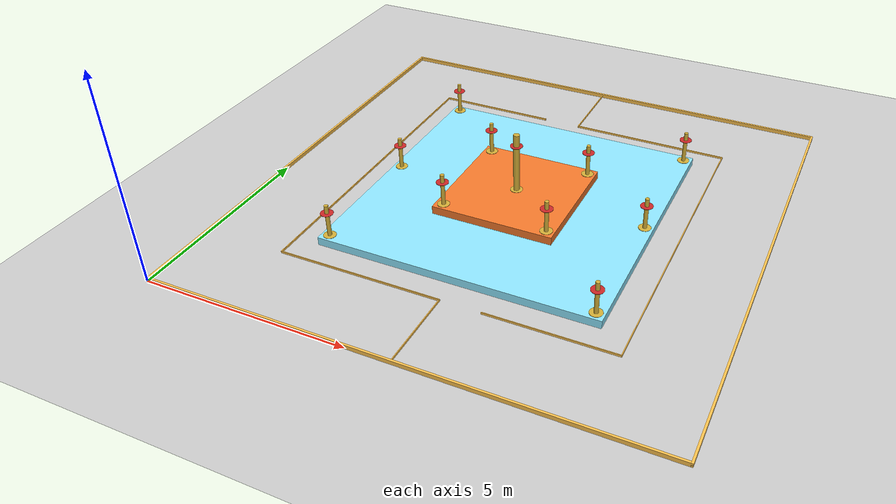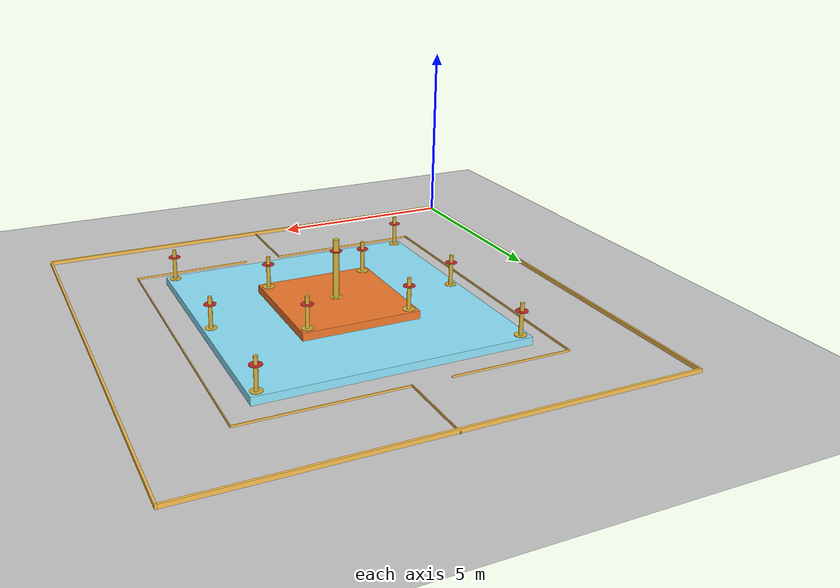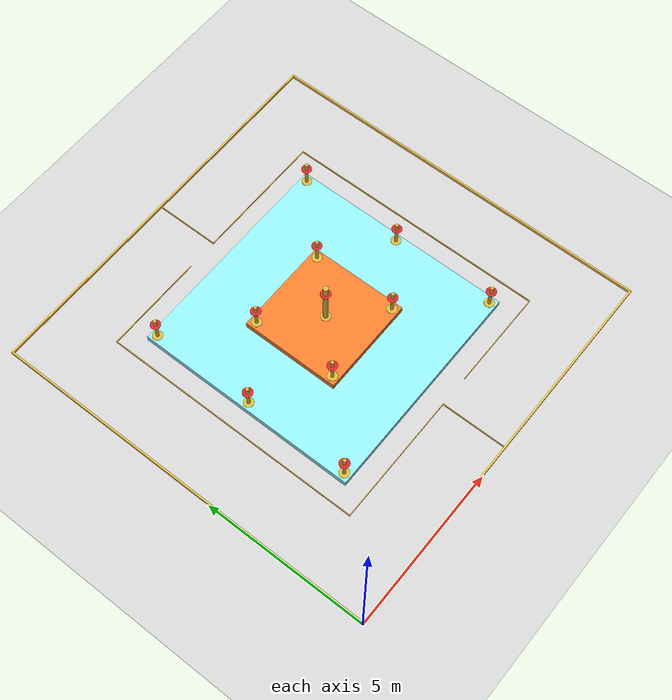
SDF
<sdf version="1.7">
 <world name="default">
  <light name="sun" type="directional">
   <pose>0 0 10 0 -0 0</pose>
   <diffuse>0.8 0.8 0.8 1</diffuse>
   <specular>0.2 0.2 0.2 1</specular>
   <attenuation>
    <range>1000</range>
    <constant>0.9</constant>
    <linear>0.01</linear>
    <quadratic>0.001</quadratic>
   </attenuation>
   <direction>-0.5 0.1 -0.9</direction>
   <spot><inner_angle>0</inner_angle><outer_angle>0</outer_angle><falloff>0</falloff></spot>
  </light>
  <model name="ground_plane">
   <static>1</static>
   <link name="link">
    <collision name="collision">
     <geometry><plane><normal>0 0 1</normal><size>100 100</size></plane></geometry>
     <surface>
      <contact><collide_bitmask>65535</collide_bitmask></contact>
      <friction><ode><mu>100</mu><mu2>50</mu2></ode></friction>
     </surface>
    </collision>
    <visual name="visual">
     <cast_shadows>0</cast_shadows>
     <geometry><plane><normal>0 0 1</normal><size>100 100</size></plane></geometry>
     <material>
      <script><uri>file://media/materials/scripts/gazebo.material</uri><name>Gazebo/Grey</name></script>
     </material>
    </visual>
   </link>
  </model>
  <gravity>0 0 -9.8</gravity>
  <magnetic_field>6e-06 2.3e-05 -4.2e-05</magnetic_field>
  <atmosphere type="adiabatic"/>
  <physics type="ode">
   <max_step_size>0.001</max_step_size>
   <real_time_factor>1</real_time_factor>
   <real_time_update_rate>1000</real_time_update_rate>
  </physics>
  <scene><ambient>0.4 0.4 0.4 1</ambient><background>0.7 0.7 0.7 1</background><shadows>1</shadows></scene>
  <spherical_coordinates>
   <surface_model>EARTH_WGS84</surface_model>
   <latitude_deg>0</latitude_deg>
   <longitude_deg>0</longitude_deg>
   <elevation>0</elevation>
   <heading_deg>0</heading_deg>
  </spherical_coordinates>
  <model name="lvl0">
   <pose>6 6 0 0 -0 0</pose>
   <link name="Wall_10">
    <collision name="Wall_10_Collision">
     <geometry><box><size>8.02 0.02 0.05</size></box></geometry>
     <pose>0 0 0.025 0 -0 0</pose>
    </collision>
    <visual name="Wall_10_Visual">
     <pose>0 0 0.025 0 -0 0</pose>
     <geometry><box><size>8.02 0.02 0.05</size></box></geometry>
     <material>
      <script><uri>file://media/materials/scripts/gazebo.material</uri><name>Gazebo/Grey</name></script>
      <ambient>1 0.764706 0.305882 1</ambient>
     </material>
     <meta><layer>0</layer></meta>
    </visual>
    <pose>-3.975 0.0075 0 0 -0 1.5708</pose>
   </link>
   <link name="Wall_12">
    <collision name="Wall_12_Collision">
     <geometry><box><size>8.02 0.02 0.05</size></box></geometry>
     <pose>0 0 0.025 0 -0 0</pose>
    </collision>
    <visual name="Wall_12_Visual">
     <pose>0 0 0.025 0 -0 0</pose>
     <geometry><box><size>8.02 0.02 0.05</size></box></geometry>
     <material>
      <script><uri>file://media/materials/scripts/gazebo.material</uri><name>Gazebo/Grey</name></script>
      <ambient>1 0.764706 0.305882 1</ambient>
     </material>
     <meta><layer>0</layer></meta>
    </visual>
    <pose>4.025 0.0075 0 0 -0 1.5708</pose>
   </link>
   <link name="Wall_14">
    <collision name="Wall_14_Collision">
     <geometry><box><size>4.02 0.02 0.05</size></box></geometry>
     <pose>0 0 0.025 0 -0 0</pose>
    </collision>
    <visual name="Wall_14_Visual">
     <pose>0 0 0.025 0 -0 0</pose>
     <geometry><box><size>4.02 0.02 0.05</size></box></geometry>
     <material>
      <script><uri>file://media/materials/scripts/gazebo.material</uri><name>Gazebo/Grey</name></script>
      <ambient>1 0.764706 0.305882 1</ambient>
     </material>
     <meta><layer>0</layer></meta>
    </visual>
    <pose>2.025 4.0075 0 0 -0 3.14159</pose>
   </link>
   <link name="Wall_16">
    <collision name="Wall_16_Collision">
     <geometry><box><size>4.02 0.02 0.05</size></box></geometry>
     <pose>0 0 0.025 0 -0 0</pose>
    </collision>
    <visual name="Wall_16_Visual">
     <pose>0 0 0.025 0 -0 0</pose>
     <geometry><box><size>4.02 0.02 0.05</size></box></geometry>
     <material>
      <script><uri>file://media/materials/scripts/gazebo.material</uri><name>Gazebo/Grey</name></script>
      <ambient>1 0.764706 0.305882 1</ambient>
     </material>
     <meta><layer>0</layer></meta>
    </visual>
    <pose>-1.975 -3.9925 0 0 -0 0</pose>
   </link>
   <link name="Wall_18">
    <collision name="Wall_18_Collision">
     <geometry><box><size>2.02 0.02 0.05</size></box></geometry>
     <pose>0 0 0.025 0 -0 0</pose>
    </collision>
    <visual name="Wall_18_Visual">
     <pose>0 0 0.025 0 -0 0</pose>
     <geometry><box><size>2.02 0.02 0.05</size></box></geometry>
     <material>
      <script><uri>file://media/materials/scripts/gazebo.material</uri><name>Gazebo/Grey</name></script>
      <ambient>1 0.764706 0.305882 1</ambient>
     </material>
     <meta><layer>0</layer></meta>
    </visual>
    <pose>0.025 5.0075 0 0 -0 1.5708</pose>
   </link>
   <link name="Wall_20">
    <collision name="Wall_20_Collision">
     <geometry><box><size>2.02 0.02 0.05</size></box></geometry>
     <pose>0 0 0.025 0 -0 0</pose>
    </collision>
    <visual name="Wall_20_Visual">
     <pose>0 0 0.025 0 -0 0</pose>
     <geometry><box><size>2.02 0.02 0.05</size></box></geometry>
     <material>
      <script><uri>file://media/materials/scripts/gazebo.material</uri><name>Gazebo/Grey</name></script>
      <ambient>1 0.764706 0.305882 1</ambient>
     </material>
     <meta><layer>0</layer></meta>
    </visual>
    <pose>0.025 -4.9925 0 0 -0 -1.5708</pose>
   </link>
   <link name="Wall_22">
    <collision name="Wall_22_Collision">
     <geometry><box><size>3.045 0.02 0.05</size></box></geometry>
     <pose>0 0 0.025 0 -0 0</pose>
    </collision>
    <visual name="Wall_22_Visual">
     <pose>0 0 0.025 0 -0 0</pose>
     <geometry><box><size>3.045 0.02 0.05</size></box></geometry>
     <material>
      <script><uri>file://media/materials/scripts/gazebo.material</uri><name>Gazebo/Grey</name></script>
      <ambient>1 0.764706 0.305882 1</ambient>
     </material>
     <meta><layer>0</layer></meta>
    </visual>
    <pose>-2.4625 4.0075 0 0 -0 0</pose>
   </link>
   <link name="Wall_24">
    <collision name="Wall_24_Collision">
     <geometry><box><size>3.045 0.02 0.05</size></box></geometry>
     <pose>0 0 0.025 0 -0 0</pose>
    </collision>
    <visual name="Wall_24_Visual">
     <pose>0 0 0.025 0 -0 0</pose>
     <geometry><box><size>3.045 0.02 0.05</size></box></geometry>
     <material>
      <script><uri>file://media/materials/scripts/gazebo.material</uri><name>Gazebo/Grey</name></script>
      <ambient>1 0.764706 0.305882 1</ambient>
     </material>
     <meta><layer>0</layer></meta>
    </visual>
    <pose>2.5125 -3.9925 0 0 -0 3.14159</pose>
   </link>
   <link name="Wall_5">
    <collision name="Wall_5_Collision">
     <geometry><box><size>12 0.05 0.1</size></box></geometry>
     <pose>0 0 0.05 0 -0 0</pose>
    </collision>
    <visual name="Wall_5_Visual">
     <pose>0 0 0.05 0 -0 0</pose>
     <geometry><box><size>12 0.05 0.1</size></box></geometry>
     <material>
      <script><uri>file://media/materials/scripts/gazebo.material</uri><name>Gazebo/Grey</name></script>
      <ambient>1 0.764706 0.305882 1</ambient>
     </material>
     <meta><layer>0</layer></meta>
    </visual>
    <pose>-5.975 -0.0175 0 0 -0 -1.5708</pose>
   </link>
   <link name="Wall_6">
    <collision name="Wall_6_Collision">
     <geometry><box><size>12 0.05 0.1</size></box></geometry>
     <pose>0 0 0.05 0 -0 0</pose>
    </collision>
    <visual name="Wall_6_Visual">
     <pose>0 0 0.05 0 -0 0</pose>
     <geometry><box><size>12 0.05 0.1</size></box></geometry>
     <material>
      <script><uri>file://media/materials/scripts/gazebo.material</uri><name>Gazebo/Grey</name></script>
      <ambient>1 0.764706 0.305882 1</ambient>
     </material>
     <meta><layer>0</layer></meta>
    </visual>
    <pose>0 -5.9925 0 0 -0 0</pose>
   </link>
   <link name="Wall_7">
    <collision name="Wall_7_Collision">
     <geometry><box><size>12 0.05 0.1</size></box></geometry>
     <pose>0 0 0.05 0 -0 0</pose>
    </collision>
    <visual name="Wall_7_Visual">
     <pose>0 0 0.05 0 -0 0</pose>
     <geometry><box><size>12 0.05 0.1</size></box></geometry>
     <material>
      <script><uri>file://media/materials/scripts/gazebo.material</uri><name>Gazebo/Grey</name></script>
      <ambient>1 0.764706 0.305882 1</ambient>
     </material>
     <meta><layer>0</layer></meta>
    </visual>
    <pose>5.975 -0.0175 0 0 -0 1.5708</pose>
   </link>
   <link name="Wall_8">
    <collision name="Wall_8_Collision">
     <geometry><box><size>12 0.05 0.1</size></box></geometry>
     <pose>0 0 0.05 0 -0 0</pose>
    </collision>
    <visual name="Wall_8_Visual">
     <pose>0 0 0.05 0 -0 0</pose>
     <geometry><box><size>12 0.05 0.1</size></box></geometry>
     <material>
      <script><uri>file://media/materials/scripts/gazebo.material</uri><name>Gazebo/Grey</name></script>
      <ambient>1 0.764706 0.305882 1</ambient>
     </material>
     <meta><layer>0</layer></meta>
    </visual>
    <pose>0 5.9575 0 0 -0 3.14159</pose>
   </link>
   <static>1</static>
  </model>
  <model name="pole_tier_1_0">
   <link name="link">
    <inertial>
     <mass>1</mass>
     <inertia><ixx>0.145833</ixx><ixy>0</ixy><ixz>0</ixz><iyy>0.145833</iyy><iyz>0</iyz><izz>0.125</izz></inertia>
    </inertial>
    <pose>0 0 0.4 0 -0 0</pose>
    <visual name="visual">
     <geometry><cylinder><radius>0.05</radius><length>0.8</length></cylinder></geometry>
     <material>
      <script><name>Gazebo/Gray</name><uri>file://media/materials/scripts/gazebo.material</uri></script>
      <shader type="pixel"><normal_map>__default__</normal_map></shader>
      <ambient>0.83 0.686 0.216 1</ambient>
      <diffuse>0.83 0.686 0.216 1</diffuse>
      <specular>0.83 0.686 0.216 1</specular>
      <emissive>0 0 0 1</emissive>
     </material>
    </visual>
    <collision name="collision">
     <geometry><cylinder><radius>0.05</radius><length>0.8</length></cylinder></geometry>
     <surface>
      <friction>
       <ode><mu>1</mu><mu2>1</mu2><fdir1>0 0 0</fdir1><slip1>0</slip1><slip2>0</slip2></ode>
       <torsional>
        <coefficient>1</coefficient>
        <patch_radius>0</patch_radius>
        <surface_radius>0</surface_radius>
        <use_patch_radius>1</use_patch_radius>
        <ode><slip>0</slip></ode>
       </torsional>
      </friction>
      <bounce><restitution_coefficient>0</restitution_coefficient><threshold>1e+06</threshold></bounce>
      <contact>
       <collide_without_contact>0</collide_without_contact>
       <collide_without_contact_bitmask>1</collide_without_contact_bitmask>
       <collide_bitmask>1</collide_bitmask>
       <ode>
        <soft_cfm>0</soft_cfm>
        <soft_erp>0.2</soft_erp>
        <kp>1e+13</kp>
        <kd>1</kd>
        <max_vel>0.01</max_vel>
        <min_depth>0</min_depth>
       </ode>
       <bullet>
        <split_impulse>1</split_impulse>
        <split_impulse_penetration_threshold>-0.01</split_impulse_penetration_threshold>
        <soft_cfm>0</soft_cfm>
        <soft_erp>0.2</soft_erp>
        <kp>1e+13</kp>
        <kd>1</kd>
       </bullet>
      </contact>
     </surface>
    </collision>
   </link>
   <link name="link_clone">
    <inertial>
     <mass>1</mass>
     <inertia><ixx>0.145833</ixx><ixy>0</ixy><ixz>0</ixz><iyy>0.145833</iyy><iyz>0</iyz><izz>0.125</izz></inertia>
    </inertial>
    <visual name="visual">
     <geometry><cylinder><radius>0.15</radius><length>0.01</length></cylinder></geometry>
     <material>
      <script><name>Gazebo/Grey</name><uri>file://media/materials/scripts/gazebo.material</uri></script>
      <shader type="pixel"><normal_map>__default__</normal_map></shader>
      <ambient>0.83 0.686 0.216 1</ambient>
      <diffuse>0.7 0.7 0.7 1</diffuse>
      <specular>0.01 0.01 0.01 1</specular>
      <emissive>0 0 0 1</emissive>
     </material>
    </visual>
    <collision name="collision">
     <geometry><cylinder><radius>0.15</radius><length>0.01</length></cylinder></geometry>
     <surface>
      <friction>
       <ode><mu>1</mu><mu2>1</mu2><fdir1>0 0 0</fdir1><slip1>0</slip1><slip2>0</slip2></ode>
       <torsional>
        <coefficient>1</coefficient>
        <patch_radius>0</patch_radius>
        <surface_radius>0</surface_radius>
        <use_patch_radius>1</use_patch_radius>
        <ode><slip>0</slip></ode>
       </torsional>
      </friction>
      <bounce><restitution_coefficient>0</restitution_coefficient><threshold>1e+06</threshold></bounce>
      <contact>
       <collide_without_contact>0</collide_without_contact>
       <collide_without_contact_bitmask>1</collide_without_contact_bitmask>
       <collide_bitmask>1</collide_bitmask>
       <ode>
        <soft_cfm>0</soft_cfm>
        <soft_erp>0.2</soft_erp>
        <kp>1e+13</kp>
        <kd>1</kd>
        <max_vel>0.01</max_vel>
        <min_depth>0</min_depth>
       </ode>
       <bullet>
        <split_impulse>1</split_impulse>
        <split_impulse_penetration_threshold>-0.01</split_impulse_penetration_threshold>
        <soft_cfm>0</soft_cfm>
        <soft_erp>0.2</soft_erp>
        <kp>1e+13</kp>
        <kd>1</kd>
       </bullet>
      </contact>
     </surface>
    </collision>
   </link>
   <link name="link_clone_clone">
    <inertial>
     <mass>1</mass>
     <inertia><ixx>0.145833</ixx><ixy>0</ixy><ixz>0</ixz><iyy>0.145833</iyy><iyz>0</iyz><izz>0.125</izz></inertia>
    </inertial>
    <pose>0 0 0.6 0 -0 0</pose>
    <visual name="visual">
     <geometry><cylinder><radius>0.15</radius><length>0.01</length></cylinder></geometry>
     <material>
      <script><name>Gazebo/Red</name><uri>file://media/materials/scripts/gazebo.material</uri></script>
      <shader type="pixel"><normal_map>__default__</normal_map></shader>
      <ambient>0.83 0.686 0.216 1</ambient>
      <diffuse>0.7 0.7 0.7 1</diffuse>
      <specular>0.01 0.01 0.01 1</specular>
      <emissive>0 0 0 1</emissive>
     </material>
    </visual>
    <collision name="collision">
     <geometry><cylinder><radius>0.15</radius><length>0.01</length></cylinder></geometry>
     <surface>
      <friction>
       <ode><mu>1</mu><mu2>1</mu2><fdir1>0 0 0</fdir1><slip1>0</slip1><slip2>0</slip2></ode>
       <torsional>
        <coefficient>1</coefficient>
        <patch_radius>0</patch_radius>
        <surface_radius>0</surface_radius>
        <use_patch_radius>1</use_patch_radius>
        <ode><slip>0</slip></ode>
       </torsional>
      </friction>
      <bounce><restitution_coefficient>0</restitution_coefficient><threshold>1e+06</threshold></bounce>
      <contact>
       <collide_without_contact>0</collide_without_contact>
       <collide_without_contact_bitmask>1</collide_without_contact_bitmask>
       <collide_bitmask>1</collide_bitmask>
       <ode>
        <soft_cfm>0</soft_cfm>
        <soft_erp>0.2</soft_erp>
        <kp>1e+13</kp>
        <kd>1</kd>
        <max_vel>0.01</max_vel>
        <min_depth>0</min_depth>
       </ode>
       <bullet>
        <split_impulse>1</split_impulse>
        <split_impulse_penetration_threshold>-0.01</split_impulse_penetration_threshold>
        <soft_cfm>0</soft_cfm>
        <soft_erp>0.2</soft_erp>
        <kp>1e+13</kp>
        <kd>1</kd>
       </bullet>
      </contact>
     </surface>
    </collision>
   </link>
   <joint name="link_JOINT_0" type="fixed">
    <parent>link</parent>
    <child>link_clone</child>
    <physics>
     <ode><limit><cfm>0</cfm><erp>0.2</erp></limit><suspension><cfm>0</cfm><erp>0.2</erp></suspension></ode>
    </physics>
   </joint>
   <joint name="link_JOINT_1" type="fixed">
    <parent>link</parent>
    <child>link_clone_clone</child>
    <physics>
     <ode><limit><cfm>0</cfm><erp>0.2</erp></limit><suspension><cfm>0</cfm><erp>0.2</erp></suspension></ode>
    </physics>
   </joint>
   <static>0</static>
   <pose>2.80206 2.79539 0.205005 1.8e-05 -2.7e-05 -0.021574</pose>
  </model>
  <model name="pole_tier_1_1">
   <link name="link">
    <inertial>
     <mass>1</mass>
     <inertia><ixx>0.145833</ixx><ixy>0</ixy><ixz>0</ixz><iyy>0.145833</iyy><iyz>0</iyz><izz>0.125</izz></inertia>
    </inertial>
    <pose>0 0 0.4 0 -0 0</pose>
    <visual name="visual">
     <geometry><cylinder><radius>0.05</radius><length>0.8</length></cylinder></geometry>
     <material>
      <script><name>Gazebo/Gray</name><uri>file://media/materials/scripts/gazebo.material</uri></script>
      <shader type="pixel"><normal_map>__default__</normal_map></shader>
      <ambient>0.83 0.686 0.216 1</ambient>
      <diffuse>0.83 0.686 0.216 1</diffuse>
      <specular>0.83 0.686 0.216 1</specular>
      <emissive>0 0 0 1</emissive>
     </material>
    </visual>
    <collision name="collision">
     <geometry><cylinder><radius>0.05</radius><length>0.8</length></cylinder></geometry>
     <surface>
      <friction>
       <ode><mu>1</mu><mu2>1</mu2><fdir1>0 0 0</fdir1><slip1>0</slip1><slip2>0</slip2></ode>
       <torsional>
        <coefficient>1</coefficient>
        <patch_radius>0</patch_radius>
        <surface_radius>0</surface_radius>
        <use_patch_radius>1</use_patch_radius>
        <ode><slip>0</slip></ode>
       </torsional>
      </friction>
      <bounce><restitution_coefficient>0</restitution_coefficient><threshold>1e+06</threshold></bounce>
      <contact>
       <collide_without_contact>0</collide_without_contact>
       <collide_without_contact_bitmask>1</collide_without_contact_bitmask>
       <collide_bitmask>1</collide_bitmask>
       <ode>
        <soft_cfm>0</soft_cfm>
        <soft_erp>0.2</soft_erp>
        <kp>1e+13</kp>
        <kd>1</kd>
        <max_vel>0.01</max_vel>
        <min_depth>0</min_depth>
       </ode>
       <bullet>
        <split_impulse>1</split_impulse>
        <split_impulse_penetration_threshold>-0.01</split_impulse_penetration_threshold>
        <soft_cfm>0</soft_cfm>
        <soft_erp>0.2</soft_erp>
        <kp>1e+13</kp>
        <kd>1</kd>
       </bullet>
      </contact>
     </surface>
    </collision>
   </link>
   <link name="link_clone">
    <inertial>
     <mass>1</mass>
     <inertia><ixx>0.145833</ixx><ixy>0</ixy><ixz>0</ixz><iyy>0.145833</iyy><iyz>0</iyz><izz>0.125</izz></inertia>
    </inertial>
    <visual name="visual">
     <geometry><cylinder><radius>0.15</radius><length>0.01</length></cylinder></geometry>
     <material>
      <script><name>Gazebo/Grey</name><uri>file://media/materials/scripts/gazebo.material</uri></script>
      <shader type="pixel"><normal_map>__default__</normal_map></shader>
      <ambient>0.83 0.686 0.216 1</ambient>
      <diffuse>0.7 0.7 0.7 1</diffuse>
      <specular>0.01 0.01 0.01 1</specular>
      <emissive>0 0 0 1</emissive>
     </material>
    </visual>
    <collision name="collision">
     <geometry><cylinder><radius>0.15</radius><length>0.01</length></cylinder></geometry>
     <surface>
      <friction>
       <ode><mu>1</mu><mu2>1</mu2><fdir1>0 0 0</fdir1><slip1>0</slip1><slip2>0</slip2></ode>
       <torsional>
        <coefficient>1</coefficient>
        <patch_radius>0</patch_radius>
        <surface_radius>0</surface_radius>
        <use_patch_radius>1</use_patch_radius>
        <ode><slip>0</slip></ode>
       </torsional>
      </friction>
      <bounce><restitution_coefficient>0</restitution_coefficient><threshold>1e+06</threshold></bounce>
      <contact>
       <collide_without_contact>0</collide_without_contact>
       <collide_without_contact_bitmask>1</collide_without_contact_bitmask>
       <collide_bitmask>1</collide_bitmask>
       <ode>
        <soft_cfm>0</soft_cfm>
        <soft_erp>0.2</soft_erp>
        <kp>1e+13</kp>
        <kd>1</kd>
        <max_vel>0.01</max_vel>
        <min_depth>0</min_depth>
       </ode>
       <bullet>
        <split_impulse>1</split_impulse>
        <split_impulse_penetration_threshold>-0.01</split_impulse_penetration_threshold>
        <soft_cfm>0</soft_cfm>
        <soft_erp>0.2</soft_erp>
        <kp>1e+13</kp>
        <kd>1</kd>
       </bullet>
      </contact>
     </surface>
    </collision>
   </link>
   <link name="link_clone_clone">
    <inertial>
     <mass>1</mass>
     <inertia><ixx>0.145833</ixx><ixy>0</ixy><ixz>0</ixz><iyy>0.145833</iyy><iyz>0</iyz><izz>0.125</izz></inertia>
    </inertial>
    <pose>0 0 0.6 0 -0 0</pose>
    <visual name="visual">
     <geometry><cylinder><radius>0.15</radius><length>0.01</length></cylinder></geometry>
     <material>
      <script><name>Gazebo/Red</name><uri>file://media/materials/scripts/gazebo.material</uri></script>
      <shader type="pixel"><normal_map>__default__</normal_map></shader>
      <ambient>0.83 0.686 0.216 1</ambient>
      <diffuse>0.7 0.7 0.7 1</diffuse>
      <specular>0.01 0.01 0.01 1</specular>
      <emissive>0 0 0 1</emissive>
     </material>
    </visual>
    <collision name="collision">
     <geometry><cylinder><radius>0.15</radius><length>0.01</length></cylinder></geometry>
     <surface>
      <friction>
       <ode><mu>1</mu><mu2>1</mu2><fdir1>0 0 0</fdir1><slip1>0</slip1><slip2>0</slip2></ode>
       <torsional>
        <coefficient>1</coefficient>
        <patch_radius>0</patch_radius>
        <surface_radius>0</surface_radius>
        <use_patch_radius>1</use_patch_radius>
        <ode><slip>0</slip></ode>
       </torsional>
      </friction>
      <bounce><restitution_coefficient>0</restitution_coefficient><threshold>1e+06</threshold></bounce>
      <contact>
       <collide_without_contact>0</collide_without_contact>
       <collide_without_contact_bitmask>1</collide_without_contact_bitmask>
       <collide_bitmask>1</collide_bitmask>
       <ode>
        <soft_cfm>0</soft_cfm>
        <soft_erp>0.2</soft_erp>
        <kp>1e+13</kp>
        <kd>1</kd>
        <max_vel>0.01</max_vel>
        <min_depth>0</min_depth>
       </ode>
       <bullet>
        <split_impulse>1</split_impulse>
        <split_impulse_penetration_threshold>-0.01</split_impulse_penetration_threshold>
        <soft_cfm>0</soft_cfm>
        <soft_erp>0.2</soft_erp>
        <kp>1e+13</kp>
        <kd>1</kd>
       </bullet>
      </contact>
     </surface>
    </collision>
   </link>
   <joint name="link_JOINT_0" type="fixed">
    <parent>link</parent>
    <child>link_clone</child>
    <physics>
     <ode><limit><cfm>0</cfm><erp>0.2</erp></limit><suspension><cfm>0</cfm><erp>0.2</erp></suspension></ode>
    </physics>
   </joint>
   <joint name="link_JOINT_1" type="fixed">
    <parent>link</parent>
    <child>link_clone_clone</child>
    <physics>
     <ode><limit><cfm>0</cfm><erp>0.2</erp></limit><suspension><cfm>0</cfm><erp>0.2</erp></suspension></ode>
    </physics>
   </joint>
   <static>0</static>
   <pose>2.80091 5.99741 0.205006 1.7e-05 -3.6e-05 -0.008457</pose>
  </model>
  <model name="pole_tier_1_2">
   <link name="link">
    <inertial>
     <mass>1</mass>
     <inertia><ixx>0.145833</ixx><ixy>0</ixy><ixz>0</ixz><iyy>0.145833</iyy><iyz>0</iyz><izz>0.125</izz></inertia>
    </inertial>
    <pose>0 0 0.4 0 -0 0</pose>
    <visual name="visual">
     <geometry><cylinder><radius>0.05</radius><length>0.8</length></cylinder></geometry>
     <material>
      <script><name>Gazebo/Gray</name><uri>file://media/materials/scripts/gazebo.material</uri></script>
      <shader type="pixel"><normal_map>__default__</normal_map></shader>
      <ambient>0.83 0.686 0.216 1</ambient>
      <diffuse>0.83 0.686 0.216 1</diffuse>
      <specular>0.83 0.686 0.216 1</specular>
      <emissive>0 0 0 1</emissive>
     </material>
    </visual>
    <collision name="collision">
     <geometry><cylinder><radius>0.05</radius><length>0.8</length></cylinder></geometry>
     <surface>
      <friction>
       <ode><mu>1</mu><mu2>1</mu2><fdir1>0 0 0</fdir1><slip1>0</slip1><slip2>0</slip2></ode>
       <torsional>
        <coefficient>1</coefficient>
        <patch_radius>0</patch_radius>
        <surface_radius>0</surface_radius>
        <use_patch_radius>1</use_patch_radius>
        <ode><slip>0</slip></ode>
       </torsional>
      </friction>
      <bounce><restitution_coefficient>0</restitution_coefficient><threshold>1e+06</threshold></bounce>
      <contact>
       <collide_without_contact>0</collide_without_contact>
       <collide_without_contact_bitmask>1</collide_without_contact_bitmask>
       <collide_bitmask>1</collide_bitmask>
       <ode>
        <soft_cfm>0</soft_cfm>
        <soft_erp>0.2</soft_erp>
        <kp>1e+13</kp>
        <kd>1</kd>
        <max_vel>0.01</max_vel>
        <min_depth>0</min_depth>
       </ode>
       <bullet>
        <split_impulse>1</split_impulse>
        <split_impulse_penetration_threshold>-0.01</split_impulse_penetration_threshold>
        <soft_cfm>0</soft_cfm>
        <soft_erp>0.2</soft_erp>
        <kp>1e+13</kp>
        <kd>1</kd>
       </bullet>
      </contact>
     </surface>
    </collision>
   </link>
   <link name="link_clone">
    <inertial>
     <mass>1</mass>
     <inertia><ixx>0.145833</ixx><ixy>0</ixy><ixz>0</ixz><iyy>0.145833</iyy><iyz>0</iyz><izz>0.125</izz></inertia>
    </inertial>
    <visual name="visual">
     <geometry><cylinder><radius>0.15</radius><length>0.01</length></cylinder></geometry>
     <material>
      <script><name>Gazebo/Grey</name><uri>file://media/materials/scripts/gazebo.material</uri></script>
      <shader type="pixel"><normal_map>__default__</normal_map></shader>
      <ambient>0.83 0.686 0.216 1</ambient>
      <diffuse>0.7 0.7 0.7 1</diffuse>
      <specular>0.01 0.01 0.01 1</specular>
      <emissive>0 0 0 1</emissive>
     </material>
    </visual>
    <collision name="collision">
     <geometry><cylinder><radius>0.15</radius><length>0.01</length></cylinder></geometry>
     <surface>
      <friction>
       <ode><mu>1</mu><mu2>1</mu2><fdir1>0 0 0</fdir1><slip1>0</slip1><slip2>0</slip2></ode>
       <torsional>
        <coefficient>1</coefficient>
        <patch_radius>0</patch_radius>
        <surface_radius>0</surface_radius>
        <use_patch_radius>1</use_patch_radius>
        <ode><slip>0</slip></ode>
       </torsional>
      </friction>
      <bounce><restitution_coefficient>0</restitution_coefficient><threshold>1e+06</threshold></bounce>
      <contact>
       <collide_without_contact>0</collide_without_contact>
       <collide_without_contact_bitmask>1</collide_without_contact_bitmask>
       <collide_bitmask>1</collide_bitmask>
       <ode>
        <soft_cfm>0</soft_cfm>
        <soft_erp>0.2</soft_erp>
        <kp>1e+13</kp>
        <kd>1</kd>
        <max_vel>0.01</max_vel>
        <min_depth>0</min_depth>
       </ode>
       <bullet>
        <split_impulse>1</split_impulse>
        <split_impulse_penetration_threshold>-0.01</split_impulse_penetration_threshold>
        <soft_cfm>0</soft_cfm>
        <soft_erp>0.2</soft_erp>
        <kp>1e+13</kp>
        <kd>1</kd>
       </bullet>
      </contact>
     </surface>
    </collision>
   </link>
   <link name="link_clone_clone">
    <inertial>
     <mass>1</mass>
     <inertia><ixx>0.145833</ixx><ixy>0</ixy><ixz>0</ixz><iyy>0.145833</iyy><iyz>0</iyz><izz>0.125</izz></inertia>
    </inertial>
    <pose>0 0 0.6 0 -0 0</pose>
    <visual name="visual">
     <geometry><cylinder><radius>0.15</radius><length>0.01</length></cylinder></geometry>
     <material>
      <script><name>Gazebo/Red</name><uri>file://media/materials/scripts/gazebo.material</uri></script>
      <shader type="pixel"><normal_map>__default__</normal_map></shader>
      <ambient>0.83 0.686 0.216 1</ambient>
      <diffuse>0.7 0.7 0.7 1</diffuse>
      <specular>0.01 0.01 0.01 1</specular>
      <emissive>0 0 0 1</emissive>
     </material>
    </visual>
    <collision name="collision">
     <geometry><cylinder><radius>0.15</radius><length>0.01</length></cylinder></geometry>
     <surface>
      <friction>
       <ode><mu>1</mu><mu2>1</mu2><fdir1>0 0 0</fdir1><slip1>0</slip1><slip2>0</slip2></ode>
       <torsional>
        <coefficient>1</coefficient>
        <patch_radius>0</patch_radius>
        <surface_radius>0</surface_radius>
        <use_patch_radius>1</use_patch_radius>
        <ode><slip>0</slip></ode>
       </torsional>
      </friction>
      <bounce><restitution_coefficient>0</restitution_coefficient><threshold>1e+06</threshold></bounce>
      <contact>
       <collide_without_contact>0</collide_without_contact>
       <collide_without_contact_bitmask>1</collide_without_contact_bitmask>
       <collide_bitmask>1</collide_bitmask>
       <ode>
        <soft_cfm>0</soft_cfm>
        <soft_erp>0.2</soft_erp>
        <kp>1e+13</kp>
        <kd>1</kd>
        <max_vel>0.01</max_vel>
        <min_depth>0</min_depth>
       </ode>
       <bullet>
        <split_impulse>1</split_impulse>
        <split_impulse_penetration_threshold>-0.01</split_impulse_penetration_threshold>
        <soft_cfm>0</soft_cfm>
        <soft_erp>0.2</soft_erp>
        <kp>1e+13</kp>
        <kd>1</kd>
       </bullet>
      </contact>
     </surface>
    </collision>
   </link>
   <joint name="link_JOINT_0" type="fixed">
    <parent>link</parent>
    <child>link_clone</child>
    <physics>
     <ode><limit><cfm>0</cfm><erp>0.2</erp></limit><suspension><cfm>0</cfm><erp>0.2</erp></suspension></ode>
    </physics>
   </joint>
   <joint name="link_JOINT_1" type="fixed">
    <parent>link</parent>
    <child>link_clone_clone</child>
    <physics>
     <ode><limit><cfm>0</cfm><erp>0.2</erp></limit><suspension><cfm>0</cfm><erp>0.2</erp></suspension></ode>
    </physics>
   </joint>
   <static>0</static>
   <pose>9.20111 9.19778 0.205004 7e-06 -2.5e-05 -0.022287</pose>
  </model>
  <model name="pole_tier_1_3">
   <link name="link">
    <inertial>
     <mass>1</mass>
     <inertia><ixx>0.145833</ixx><ixy>0</ixy><ixz>0</ixz><iyy>0.145833</iyy><iyz>0</iyz><izz>0.125</izz></inertia>
    </inertial>
    <pose>0 0 0.4 0 -0 0</pose>
    <visual name="visual">
     <geometry><cylinder><radius>0.05</radius><length>0.8</length></cylinder></geometry>
     <material>
      <script><name>Gazebo/Gray</name><uri>file://media/materials/scripts/gazebo.material</uri></script>
      <shader type="pixel"><normal_map>__default__</normal_map></shader>
      <ambient>0.83 0.686 0.216 1</ambient>
      <diffuse>0.83 0.686 0.216 1</diffuse>
      <specular>0.83 0.686 0.216 1</specular>
      <emissive>0 0 0 1</emissive>
     </material>
    </visual>
    <collision name="collision">
     <geometry><cylinder><radius>0.05</radius><length>0.8</length></cylinder></geometry>
     <surface>
      <friction>
       <ode><mu>1</mu><mu2>1</mu2><fdir1>0 0 0</fdir1><slip1>0</slip1><slip2>0</slip2></ode>
       <torsional>
        <coefficient>1</coefficient>
        <patch_radius>0</patch_radius>
        <surface_radius>0</surface_radius>
        <use_patch_radius>1</use_patch_radius>
        <ode><slip>0</slip></ode>
       </torsional>
      </friction>
      <bounce><restitution_coefficient>0</restitution_coefficient><threshold>1e+06</threshold></bounce>
      <contact>
       <collide_without_contact>0</collide_without_contact>
       <collide_without_contact_bitmask>1</collide_without_contact_bitmask>
       <collide_bitmask>1</collide_bitmask>
       <ode>
        <soft_cfm>0</soft_cfm>
        <soft_erp>0.2</soft_erp>
        <kp>1e+13</kp>
        <kd>1</kd>
        <max_vel>0.01</max_vel>
        <min_depth>0</min_depth>
       </ode>
       <bullet>
        <split_impulse>1</split_impulse>
        <split_impulse_penetration_threshold>-0.01</split_impulse_penetration_threshold>
        <soft_cfm>0</soft_cfm>
        <soft_erp>0.2</soft_erp>
        <kp>1e+13</kp>
        <kd>1</kd>
       </bullet>
      </contact>
     </surface>
    </collision>
   </link>
   <link name="link_clone">
    <inertial>
     <mass>1</mass>
     <inertia><ixx>0.145833</ixx><ixy>0</ixy><ixz>0</ixz><iyy>0.145833</iyy><iyz>0</iyz><izz>0.125</izz></inertia>
    </inertial>
    <visual name="visual">
     <geometry><cylinder><radius>0.15</radius><length>0.01</length></cylinder></geometry>
     <material>
      <script><name>Gazebo/Grey</name><uri>file://media/materials/scripts/gazebo.material</uri></script>
      <shader type="pixel"><normal_map>__default__</normal_map></shader>
      <ambient>0.83 0.686 0.216 1</ambient>
      <diffuse>0.7 0.7 0.7 1</diffuse>
      <specular>0.01 0.01 0.01 1</specular>
      <emissive>0 0 0 1</emissive>
     </material>
    </visual>
    <collision name="collision">
     <geometry><cylinder><radius>0.15</radius><length>0.01</length></cylinder></geometry>
     <surface>
      <friction>
       <ode><mu>1</mu><mu2>1</mu2><fdir1>0 0 0</fdir1><slip1>0</slip1><slip2>0</slip2></ode>
       <torsional>
        <coefficient>1</coefficient>
        <patch_radius>0</patch_radius>
        <surface_radius>0</surface_radius>
        <use_patch_radius>1</use_patch_radius>
        <ode><slip>0</slip></ode>
       </torsional>
      </friction>
      <bounce><restitution_coefficient>0</restitution_coefficient><threshold>1e+06</threshold></bounce>
      <contact>
       <collide_without_contact>0</collide_without_contact>
       <collide_without_contact_bitmask>1</collide_without_contact_bitmask>
       <collide_bitmask>1</collide_bitmask>
       <ode>
        <soft_cfm>0</soft_cfm>
        <soft_erp>0.2</soft_erp>
        <kp>1e+13</kp>
        <kd>1</kd>
        <max_vel>0.01</max_vel>
        <min_depth>0</min_depth>
       </ode>
       <bullet>
        <split_impulse>1</split_impulse>
        <split_impulse_penetration_threshold>-0.01</split_impulse_penetration_threshold>
        <soft_cfm>0</soft_cfm>
        <soft_erp>0.2</soft_erp>
        <kp>1e+13</kp>
        <kd>1</kd>
       </bullet>
      </contact>
     </surface>
    </collision>
   </link>
   <link name="link_clone_clone">
    <inertial>
     <mass>1</mass>
     <inertia><ixx>0.145833</ixx><ixy>0</ixy><ixz>0</ixz><iyy>0.145833</iyy><iyz>0</iyz><izz>0.125</izz></inertia>
    </inertial>
    <pose>0 0 0.6 0 -0 0</pose>
    <visual name="visual">
     <geometry><cylinder><radius>0.15</radius><length>0.01</length></cylinder></geometry>
     <material>
      <script><name>Gazebo/Red</name><uri>file://media/materials/scripts/gazebo.material</uri></script>
      <shader type="pixel"><normal_map>__default__</normal_map></shader>
      <ambient>0.83 0.686 0.216 1</ambient>
      <diffuse>0.7 0.7 0.7 1</diffuse>
      <specular>0.01 0.01 0.01 1</specular>
      <emissive>0 0 0 1</emissive>
     </material>
    </visual>
    <collision name="collision">
     <geometry><cylinder><radius>0.15</radius><length>0.01</length></cylinder></geometry>
     <surface>
      <friction>
       <ode><mu>1</mu><mu2>1</mu2><fdir1>0 0 0</fdir1><slip1>0</slip1><slip2>0</slip2></ode>
       <torsional>
        <coefficient>1</coefficient>
        <patch_radius>0</patch_radius>
        <surface_radius>0</surface_radius>
        <use_patch_radius>1</use_patch_radius>
        <ode><slip>0</slip></ode>
       </torsional>
      </friction>
      <bounce><restitution_coefficient>0</restitution_coefficient><threshold>1e+06</threshold></bounce>
      <contact>
       <collide_without_contact>0</collide_without_contact>
       <collide_without_contact_bitmask>1</collide_without_contact_bitmask>
       <collide_bitmask>1</collide_bitmask>
       <ode>
        <soft_cfm>0</soft_cfm>
        <soft_erp>0.2</soft_erp>
        <kp>1e+13</kp>
        <kd>1</kd>
        <max_vel>0.01</max_vel>
        <min_depth>0</min_depth>
       </ode>
       <bullet>
        <split_impulse>1</split_impulse>
        <split_impulse_penetration_threshold>-0.01</split_impulse_penetration_threshold>
        <soft_cfm>0</soft_cfm>
        <soft_erp>0.2</soft_erp>
        <kp>1e+13</kp>
        <kd>1</kd>
       </bullet>
      </contact>
     </surface>
    </collision>
   </link>
   <joint name="link_JOINT_0" type="fixed">
    <parent>link</parent>
    <child>link_clone</child>
    <physics>
     <ode><limit><cfm>0</cfm><erp>0.2</erp></limit><suspension><cfm>0</cfm><erp>0.2</erp></suspension></ode>
    </physics>
   </joint>
   <joint name="link_JOINT_1" type="fixed">
    <parent>link</parent>
    <child>link_clone_clone</child>
    <physics>
     <ode><limit><cfm>0</cfm><erp>0.2</erp></limit><suspension><cfm>0</cfm><erp>0.2</erp></suspension></ode>
    </physics>
   </joint>
   <static>0</static>
   <pose>2.80158 9.19959 0.205 4e-06 0 -0.007982</pose>
  </model>
  <model name="pole_tier_1_5">
   <link name="link">
    <inertial>
     <mass>1</mass>
     <inertia><ixx>0.145833</ixx><ixy>0</ixy><ixz>0</ixz><iyy>0.145833</iyy><iyz>0</iyz><izz>0.125</izz></inertia>
    </inertial>
    <pose>0 0 0.4 0 -0 0</pose>
    <visual name="visual">
     <geometry><cylinder><radius>0.05</radius><length>0.8</length></cylinder></geometry>
     <material>
      <script><name>Gazebo/Gray</name><uri>file://media/materials/scripts/gazebo.material</uri></script>
      <shader type="pixel"><normal_map>__default__</normal_map></shader>
      <ambient>0.83 0.686 0.216 1</ambient>
      <diffuse>0.83 0.686 0.216 1</diffuse>
      <specular>0.83 0.686 0.216 1</specular>
      <emissive>0 0 0 1</emissive>
     </material>
    </visual>
    <collision name="collision">
     <geometry><cylinder><radius>0.05</radius><length>0.8</length></cylinder></geometry>
     <surface>
      <friction>
       <ode><mu>1</mu><mu2>1</mu2><fdir1>0 0 0</fdir1><slip1>0</slip1><slip2>0</slip2></ode>
       <torsional>
        <coefficient>1</coefficient>
        <patch_radius>0</patch_radius>
        <surface_radius>0</surface_radius>
        <use_patch_radius>1</use_patch_radius>
        <ode><slip>0</slip></ode>
       </torsional>
      </friction>
      <bounce><restitution_coefficient>0</restitution_coefficient><threshold>1e+06</threshold></bounce>
      <contact>
       <collide_without_contact>0</collide_without_contact>
       <collide_without_contact_bitmask>1</collide_without_contact_bitmask>
       <collide_bitmask>1</collide_bitmask>
       <ode>
        <soft_cfm>0</soft_cfm>
        <soft_erp>0.2</soft_erp>
        <kp>1e+13</kp>
        <kd>1</kd>
        <max_vel>0.01</max_vel>
        <min_depth>0</min_depth>
       </ode>
       <bullet>
        <split_impulse>1</split_impulse>
        <split_impulse_penetration_threshold>-0.01</split_impulse_penetration_threshold>
        <soft_cfm>0</soft_cfm>
        <soft_erp>0.2</soft_erp>
        <kp>1e+13</kp>
        <kd>1</kd>
       </bullet>
      </contact>
     </surface>
    </collision>
   </link>
   <link name="link_clone">
    <inertial>
     <mass>1</mass>
     <inertia><ixx>0.145833</ixx><ixy>0</ixy><ixz>0</ixz><iyy>0.145833</iyy><iyz>0</iyz><izz>0.125</izz></inertia>
    </inertial>
    <visual name="visual">
     <geometry><cylinder><radius>0.15</radius><length>0.01</length></cylinder></geometry>
     <material>
      <script><name>Gazebo/Grey</name><uri>file://media/materials/scripts/gazebo.material</uri></script>
      <shader type="pixel"><normal_map>__default__</normal_map></shader>
      <ambient>0.83 0.686 0.216 1</ambient>
      <diffuse>0.7 0.7 0.7 1</diffuse>
      <specular>0.01 0.01 0.01 1</specular>
      <emissive>0 0 0 1</emissive>
     </material>
    </visual>
    <collision name="collision">
     <geometry><cylinder><radius>0.15</radius><length>0.01</length></cylinder></geometry>
     <surface>
      <friction>
       <ode><mu>1</mu><mu2>1</mu2><fdir1>0 0 0</fdir1><slip1>0</slip1><slip2>0</slip2></ode>
       <torsional>
        <coefficient>1</coefficient>
        <patch_radius>0</patch_radius>
        <surface_radius>0</surface_radius>
        <use_patch_radius>1</use_patch_radius>
        <ode><slip>0</slip></ode>
       </torsional>
      </friction>
      <bounce><restitution_coefficient>0</restitution_coefficient><threshold>1e+06</threshold></bounce>
      <contact>
       <collide_without_contact>0</collide_without_contact>
       <collide_without_contact_bitmask>1</collide_without_contact_bitmask>
       <collide_bitmask>1</collide_bitmask>
       <ode>
        <soft_cfm>0</soft_cfm>
        <soft_erp>0.2</soft_erp>
        <kp>1e+13</kp>
        <kd>1</kd>
        <max_vel>0.01</max_vel>
        <min_depth>0</min_depth>
       </ode>
       <bullet>
        <split_impulse>1</split_impulse>
        <split_impulse_penetration_threshold>-0.01</split_impulse_penetration_threshold>
        <soft_cfm>0</soft_cfm>
        <soft_erp>0.2</soft_erp>
        <kp>1e+13</kp>
        <kd>1</kd>
       </bullet>
      </contact>
     </surface>
    </collision>
   </link>
   <link name="link_clone_clone">
    <inertial>
     <mass>1</mass>
     <inertia><ixx>0.145833</ixx><ixy>0</ixy><ixz>0</ixz><iyy>0.145833</iyy><iyz>0</iyz><izz>0.125</izz></inertia>
    </inertial>
    <pose>0 0 0.6 0 -0 0</pose>
    <visual name="visual">
     <geometry><cylinder><radius>0.15</radius><length>0.01</length></cylinder></geometry>
     <material>
      <script><name>Gazebo/Red</name><uri>file://media/materials/scripts/gazebo.material</uri></script>
      <shader type="pixel"><normal_map>__default__</normal_map></shader>
      <ambient>0.83 0.686 0.216 1</ambient>
      <diffuse>0.7 0.7 0.7 1</diffuse>
      <specular>0.01 0.01 0.01 1</specular>
      <emissive>0 0 0 1</emissive>
     </material>
    </visual>
    <collision name="collision">
     <geometry><cylinder><radius>0.15</radius><length>0.01</length></cylinder></geometry>
     <surface>
      <friction>
       <ode><mu>1</mu><mu2>1</mu2><fdir1>0 0 0</fdir1><slip1>0</slip1><slip2>0</slip2></ode>
       <torsional>
        <coefficient>1</coefficient>
        <patch_radius>0</patch_radius>
        <surface_radius>0</surface_radius>
        <use_patch_radius>1</use_patch_radius>
        <ode><slip>0</slip></ode>
       </torsional>
      </friction>
      <bounce><restitution_coefficient>0</restitution_coefficient><threshold>1e+06</threshold></bounce>
      <contact>
       <collide_without_contact>0</collide_without_contact>
       <collide_without_contact_bitmask>1</collide_without_contact_bitmask>
       <collide_bitmask>1</collide_bitmask>
       <ode>
        <soft_cfm>0</soft_cfm>
        <soft_erp>0.2</soft_erp>
        <kp>1e+13</kp>
        <kd>1</kd>
        <max_vel>0.01</max_vel>
        <min_depth>0</min_depth>
       </ode>
       <bullet>
        <split_impulse>1</split_impulse>
        <split_impulse_penetration_threshold>-0.01</split_impulse_penetration_threshold>
        <soft_cfm>0</soft_cfm>
        <soft_erp>0.2</soft_erp>
        <kp>1e+13</kp>
        <kd>1</kd>
       </bullet>
      </contact>
     </surface>
    </collision>
   </link>
   <joint name="link_JOINT_0" type="fixed">
    <parent>link</parent>
    <child>link_clone</child>
    <physics>
     <ode><limit><cfm>0</cfm><erp>0.2</erp></limit><suspension><cfm>0</cfm><erp>0.2</erp></suspension></ode>
    </physics>
   </joint>
   <joint name="link_JOINT_1" type="fixed">
    <parent>link</parent>
    <child>link_clone_clone</child>
    <physics>
     <ode><limit><cfm>0</cfm><erp>0.2</erp></limit><suspension><cfm>0</cfm><erp>0.2</erp></suspension></ode>
    </physics>
   </joint>
   <static>0</static>
   <pose>9.2004 5.99751 0.204996 -7e-06 -4e-05 -0.017491</pose>
  </model>
  <model name="pole_tier_1_6">
   <link name="link">
    <inertial>
     <mass>1</mass>
     <inertia><ixx>0.145833</ixx><ixy>0</ixy><ixz>0</ixz><iyy>0.145833</iyy><iyz>0</iyz><izz>0.125</izz></inertia>
    </inertial>
    <pose>0 0 0.4 0 -0 0</pose>
    <visual name="visual">
     <geometry><cylinder><radius>0.05</radius><length>0.8</length></cylinder></geometry>
     <material>
      <script><name>Gazebo/Gray</name><uri>file://media/materials/scripts/gazebo.material</uri></script>
      <shader type="pixel"><normal_map>__default__</normal_map></shader>
      <ambient>0.83 0.686 0.216 1</ambient>
      <diffuse>0.83 0.686 0.216 1</diffuse>
      <specular>0.83 0.686 0.216 1</specular>
      <emissive>0 0 0 1</emissive>
     </material>
    </visual>
    <collision name="collision">
     <geometry><cylinder><radius>0.05</radius><length>0.8</length></cylinder></geometry>
     <surface>
      <friction>
       <ode><mu>1</mu><mu2>1</mu2><fdir1>0 0 0</fdir1><slip1>0</slip1><slip2>0</slip2></ode>
       <torsional>
        <coefficient>1</coefficient>
        <patch_radius>0</patch_radius>
        <surface_radius>0</surface_radius>
        <use_patch_radius>1</use_patch_radius>
        <ode><slip>0</slip></ode>
       </torsional>
      </friction>
      <bounce><restitution_coefficient>0</restitution_coefficient><threshold>1e+06</threshold></bounce>
      <contact>
       <collide_without_contact>0</collide_without_contact>
       <collide_without_contact_bitmask>1</collide_without_contact_bitmask>
       <collide_bitmask>1</collide_bitmask>
       <ode>
        <soft_cfm>0</soft_cfm>
        <soft_erp>0.2</soft_erp>
        <kp>1e+13</kp>
        <kd>1</kd>
        <max_vel>0.01</max_vel>
        <min_depth>0</min_depth>
       </ode>
       <bullet>
        <split_impulse>1</split_impulse>
        <split_impulse_penetration_threshold>-0.01</split_impulse_penetration_threshold>
        <soft_cfm>0</soft_cfm>
        <soft_erp>0.2</soft_erp>
        <kp>1e+13</kp>
        <kd>1</kd>
       </bullet>
      </contact>
     </surface>
    </collision>
   </link>
   <link name="link_clone">
    <inertial>
     <mass>1</mass>
     <inertia><ixx>0.145833</ixx><ixy>0</ixy><ixz>0</ixz><iyy>0.145833</iyy><iyz>0</iyz><izz>0.125</izz></inertia>
    </inertial>
    <visual name="visual">
     <geometry><cylinder><radius>0.15</radius><length>0.01</length></cylinder></geometry>
     <material>
      <script><name>Gazebo/Grey</name><uri>file://media/materials/scripts/gazebo.material</uri></script>
      <shader type="pixel"><normal_map>__default__</normal_map></shader>
      <ambient>0.83 0.686 0.216 1</ambient>
      <diffuse>0.7 0.7 0.7 1</diffuse>
      <specular>0.01 0.01 0.01 1</specular>
      <emissive>0 0 0 1</emissive>
     </material>
    </visual>
    <collision name="collision">
     <geometry><cylinder><radius>0.15</radius><length>0.01</length></cylinder></geometry>
     <surface>
      <friction>
       <ode><mu>1</mu><mu2>1</mu2><fdir1>0 0 0</fdir1><slip1>0</slip1><slip2>0</slip2></ode>
       <torsional>
        <coefficient>1</coefficient>
        <patch_radius>0</patch_radius>
        <surface_radius>0</surface_radius>
        <use_patch_radius>1</use_patch_radius>
        <ode><slip>0</slip></ode>
       </torsional>
      </friction>
      <bounce><restitution_coefficient>0</restitution_coefficient><threshold>1e+06</threshold></bounce>
      <contact>
       <collide_without_contact>0</collide_without_contact>
       <collide_without_contact_bitmask>1</collide_without_contact_bitmask>
       <collide_bitmask>1</collide_bitmask>
       <ode>
        <soft_cfm>0</soft_cfm>
        <soft_erp>0.2</soft_erp>
        <kp>1e+13</kp>
        <kd>1</kd>
        <max_vel>0.01</max_vel>
        <min_depth>0</min_depth>
       </ode>
       <bullet>
        <split_impulse>1</split_impulse>
        <split_impulse_penetration_threshold>-0.01</split_impulse_penetration_threshold>
        <soft_cfm>0</soft_cfm>
        <soft_erp>0.2</soft_erp>
        <kp>1e+13</kp>
        <kd>1</kd>
       </bullet>
      </contact>
     </surface>
    </collision>
   </link>
   <link name="link_clone_clone">
    <inertial>
     <mass>1</mass>
     <inertia><ixx>0.145833</ixx><ixy>0</ixy><ixz>0</ixz><iyy>0.145833</iyy><iyz>0</iyz><izz>0.125</izz></inertia>
    </inertial>
    <pose>0 0 0.6 0 -0 0</pose>
    <visual name="visual">
     <geometry><cylinder><radius>0.15</radius><length>0.01</length></cylinder></geometry>
     <material>
      <script><name>Gazebo/Red</name><uri>file://media/materials/scripts/gazebo.material</uri></script>
      <shader type="pixel"><normal_map>__default__</normal_map></shader>
      <ambient>0.83 0.686 0.216 1</ambient>
      <diffuse>0.7 0.7 0.7 1</diffuse>
      <specular>0.01 0.01 0.01 1</specular>
      <emissive>0 0 0 1</emissive>
     </material>
    </visual>
    <collision name="collision">
     <geometry><cylinder><radius>0.15</radius><length>0.01</length></cylinder></geometry>
     <surface>
      <friction>
       <ode><mu>1</mu><mu2>1</mu2><fdir1>0 0 0</fdir1><slip1>0</slip1><slip2>0</slip2></ode>
       <torsional>
        <coefficient>1</coefficient>
        <patch_radius>0</patch_radius>
        <surface_radius>0</surface_radius>
        <use_patch_radius>1</use_patch_radius>
        <ode><slip>0</slip></ode>
       </torsional>
      </friction>
      <bounce><restitution_coefficient>0</restitution_coefficient><threshold>1e+06</threshold></bounce>
      <contact>
       <collide_without_contact>0</collide_without_contact>
       <collide_without_contact_bitmask>1</collide_without_contact_bitmask>
       <collide_bitmask>1</collide_bitmask>
       <ode>
        <soft_cfm>0</soft_cfm>
        <soft_erp>0.2</soft_erp>
        <kp>1e+13</kp>
        <kd>1</kd>
        <max_vel>0.01</max_vel>
        <min_depth>0</min_depth>
       </ode>
       <bullet>
        <split_impulse>1</split_impulse>
        <split_impulse_penetration_threshold>-0.01</split_impulse_penetration_threshold>
        <soft_cfm>0</soft_cfm>
        <soft_erp>0.2</soft_erp>
        <kp>1e+13</kp>
        <kd>1</kd>
       </bullet>
      </contact>
     </surface>
    </collision>
   </link>
   <joint name="link_JOINT_0" type="fixed">
    <parent>link</parent>
    <child>link_clone</child>
    <physics>
     <ode><limit><cfm>0</cfm><erp>0.2</erp></limit><suspension><cfm>0</cfm><erp>0.2</erp></suspension></ode>
    </physics>
   </joint>
   <joint name="link_JOINT_1" type="fixed">
    <parent>link</parent>
    <child>link_clone_clone</child>
    <physics>
     <ode><limit><cfm>0</cfm><erp>0.2</erp></limit><suspension><cfm>0</cfm><erp>0.2</erp></suspension></ode>
    </physics>
   </joint>
   <static>0</static>
   <pose>9.19959 2.80084 0.205004 6e-06 2.3e-05 0.002784</pose>
  </model>
  <model name="lvl1,2">
   <link name="link">
    <inertial>
     <mass>100</mass>
     <inertia>
      <ixx>0.166667</ixx>
      <ixy>0</ixy>
      <ixz>0</ixz>
      <iyy>0.166667</iyy>
      <iyz>0</iyz>
      <izz>0.166667</izz>
     </inertia>
    </inertial>
    <pose>0 0 0.3 0 -0 0</pose>
    <visual name="visual">
     <geometry><box><size>3 3 0.2</size></box></geometry>
     <material>
      <script><name>Gazebo/Grey</name><uri>file://media/materials/scripts/gazebo.material</uri></script>
      <shader type="pixel"><normal_map>__default__</normal_map></shader>
      <ambient>0.96 0.474 0.168 1</ambient>
      <diffuse>0.7 0.7 0.7 1</diffuse>
      <specular>0.01 0.01 0.01 1</specular>
      <emissive>0 0 0 1</emissive>
     </material>
    </visual>
    <collision name="collision">
     <geometry><box><size>3 3 0.2</size></box></geometry>
     <surface>
      <friction>
       <ode><mu>1</mu><mu2>1</mu2><fdir1>0 0 0</fdir1><slip1>0</slip1><slip2>0</slip2></ode>
       <torsional>
        <coefficient>1</coefficient>
        <patch_radius>0</patch_radius>
        <surface_radius>0</surface_radius>
        <use_patch_radius>1</use_patch_radius>
        <ode><slip>0</slip></ode>
       </torsional>
      </friction>
      <bounce><restitution_coefficient>0</restitution_coefficient><threshold>1e+06</threshold></bounce>
      <contact>
       <collide_without_contact>0</collide_without_contact>
       <collide_without_contact_bitmask>1</collide_without_contact_bitmask>
       <collide_bitmask>1</collide_bitmask>
       <ode>
        <soft_cfm>0</soft_cfm>
        <soft_erp>0.2</soft_erp>
        <kp>1e+13</kp>
        <kd>1</kd>
        <max_vel>0.01</max_vel>
        <min_depth>0</min_depth>
       </ode>
       <bullet>
        <split_impulse>1</split_impulse>
        <split_impulse_penetration_threshold>-0.01</split_impulse_penetration_threshold>
        <soft_cfm>0</soft_cfm>
        <soft_erp>0.2</soft_erp>
        <kp>1e+13</kp>
        <kd>1</kd>
       </bullet>
      </contact>
     </surface>
    </collision>
   </link>
   <link name="link_0">
    <inertial>
     <mass>1</mass>
     <inertia>
      <ixx>0.166667</ixx>
      <ixy>0</ixy>
      <ixz>0</ixz>
      <iyy>0.166667</iyy>
      <iyz>0</iyz>
      <izz>0.166667</izz>
     </inertia>
    </inertial>
    <pose>0 0 0.1 0 -0 0</pose>
    <visual name="visual">
     <geometry><box><size>6.8 6.8 0.2</size></box></geometry>
     <material>
      <lighting>1</lighting>
      <script><uri>file://media/materials/scripts/gazebo.material</uri><name>Gazebo/Grey</name></script>
      <shader type="pixel"><normal_map>__default__</normal_map></shader>
      <ambient>0.56 0.905 1 1</ambient>
      <diffuse>0.7 0.7 0.7 1</diffuse>
      <specular>0.01 0.01 0.01 1</specular>
      <emissive>0 0 0 1</emissive>
     </material>
    </visual>
    <collision name="collision">
     <geometry><box><size>6.8 6.8 0.2</size></box></geometry>
     <surface>
      <friction>
       <ode><mu>1</mu><mu2>1</mu2><fdir1>0 0 0</fdir1><slip1>0</slip1><slip2>0</slip2></ode>
       <torsional>
        <coefficient>1</coefficient>
        <patch_radius>0</patch_radius>
        <surface_radius>0</surface_radius>
        <use_patch_radius>1</use_patch_radius>
        <ode><slip>0</slip></ode>
       </torsional>
      </friction>
      <bounce><restitution_coefficient>0</restitution_coefficient><threshold>1e+06</threshold></bounce>
      <contact>
       <collide_without_contact>0</collide_without_contact>
       <collide_without_contact_bitmask>1</collide_without_contact_bitmask>
       <collide_bitmask>1</collide_bitmask>
       <ode>
        <soft_cfm>0</soft_cfm>
        <soft_erp>0.2</soft_erp>
        <kp>1e+13</kp>
        <kd>1</kd>
        <max_vel>0.01</max_vel>
        <min_depth>0</min_depth>
       </ode>
       <bullet>
        <split_impulse>1</split_impulse>
        <split_impulse_penetration_threshold>-0.01</split_impulse_penetration_threshold>
        <soft_cfm>0</soft_cfm>
        <soft_erp>0.2</soft_erp>
        <kp>1e+13</kp>
        <kd>1</kd>
       </bullet>
      </contact>
     </surface>
    </collision>
   </link>
   <joint name="link_0_JOINT_0" type="fixed">
    <parent>link_0</parent>
    <child>link</child>
    <physics>
     <ode><limit><cfm>0</cfm><erp>0.2</erp></limit><suspension><cfm>0</cfm><erp>0.2</erp></suspension></ode>
    </physics>
   </joint>
   <static>1</static>
   <pose>6 6 0 0 -0 0</pose>
  </model>
  <model name="pole_tier_1">
   <link name="link">
    <inertial>
     <mass>1</mass>
     <inertia><ixx>0.145833</ixx><ixy>0</ixy><ixz>0</ixz><iyy>0.145833</iyy><iyz>0</iyz><izz>0.125</izz></inertia>
    </inertial>
    <pose>0 0 0.4 0 -0 0</pose>
    <visual name="visual">
     <geometry><cylinder><radius>0.05</radius><length>0.8</length></cylinder></geometry>
     <material>
      <script><name>Gazebo/Gray</name><uri>file://media/materials/scripts/gazebo.material</uri></script>
      <shader type="pixel"><normal_map>__default__</normal_map></shader>
      <ambient>0.83 0.686 0.216 1</ambient>
      <diffuse>0.83 0.686 0.216 1</diffuse>
      <specular>0.83 0.686 0.216 1</specular>
      <emissive>0 0 0 1</emissive>
     </material>
    </visual>
    <collision name="collision">
     <geometry><cylinder><radius>0.05</radius><length>0.8</length></cylinder></geometry>
     <surface>
      <friction>
       <ode><mu>1</mu><mu2>1</mu2><fdir1>0 0 0</fdir1><slip1>0</slip1><slip2>0</slip2></ode>
       <torsional>
        <coefficient>1</coefficient>
        <patch_radius>0</patch_radius>
        <surface_radius>0</surface_radius>
        <use_patch_radius>1</use_patch_radius>
        <ode><slip>0</slip></ode>
       </torsional>
      </friction>
      <bounce><restitution_coefficient>0</restitution_coefficient><threshold>1e+06</threshold></bounce>
      <contact>
       <collide_without_contact>0</collide_without_contact>
       <collide_without_contact_bitmask>1</collide_without_contact_bitmask>
       <collide_bitmask>1</collide_bitmask>
       <ode>
        <soft_cfm>0</soft_cfm>
        <soft_erp>0.2</soft_erp>
        <kp>1e+13</kp>
        <kd>1</kd>
        <max_vel>0.01</max_vel>
        <min_depth>0</min_depth>
       </ode>
       <bullet>
        <split_impulse>1</split_impulse>
        <split_impulse_penetration_threshold>-0.01</split_impulse_penetration_threshold>
        <soft_cfm>0</soft_cfm>
        <soft_erp>0.2</soft_erp>
        <kp>1e+13</kp>
        <kd>1</kd>
       </bullet>
      </contact>
     </surface>
    </collision>
   </link>
   <link name="link_clone">
    <inertial>
     <mass>1</mass>
     <inertia><ixx>0.145833</ixx><ixy>0</ixy><ixz>0</ixz><iyy>0.145833</iyy><iyz>0</iyz><izz>0.125</izz></inertia>
    </inertial>
    <visual name="visual">
     <geometry><cylinder><radius>0.15</radius><length>0.01</length></cylinder></geometry>
     <material>
      <script><name>Gazebo/Grey</name><uri>file://media/materials/scripts/gazebo.material</uri></script>
      <shader type="pixel"><normal_map>__default__</normal_map></shader>
      <ambient>0.83 0.686 0.216 1</ambient>
      <diffuse>0.7 0.7 0.7 1</diffuse>
      <specular>0.01 0.01 0.01 1</specular>
      <emissive>0 0 0 1</emissive>
     </material>
    </visual>
    <collision name="collision">
     <geometry><cylinder><radius>0.15</radius><length>0.01</length></cylinder></geometry>
     <surface>
      <friction>
       <ode><mu>1</mu><mu2>1</mu2><fdir1>0 0 0</fdir1><slip1>0</slip1><slip2>0</slip2></ode>
       <torsional>
        <coefficient>1</coefficient>
        <patch_radius>0</patch_radius>
        <surface_radius>0</surface_radius>
        <use_patch_radius>1</use_patch_radius>
        <ode><slip>0</slip></ode>
       </torsional>
      </friction>
      <bounce><restitution_coefficient>0</restitution_coefficient><threshold>1e+06</threshold></bounce>
      <contact>
       <collide_without_contact>0</collide_without_contact>
       <collide_without_contact_bitmask>1</collide_without_contact_bitmask>
       <collide_bitmask>1</collide_bitmask>
       <ode>
        <soft_cfm>0</soft_cfm>
        <soft_erp>0.2</soft_erp>
        <kp>1e+13</kp>
        <kd>1</kd>
        <max_vel>0.01</max_vel>
        <min_depth>0</min_depth>
       </ode>
       <bullet>
        <split_impulse>1</split_impulse>
        <split_impulse_penetration_threshold>-0.01</split_impulse_penetration_threshold>
        <soft_cfm>0</soft_cfm>
        <soft_erp>0.2</soft_erp>
        <kp>1e+13</kp>
        <kd>1</kd>
       </bullet>
      </contact>
     </surface>
    </collision>
   </link>
   <link name="link_clone_clone">
    <inertial>
     <mass>1</mass>
     <inertia><ixx>0.145833</ixx><ixy>0</ixy><ixz>0</ixz><iyy>0.145833</iyy><iyz>0</iyz><izz>0.125</izz></inertia>
    </inertial>
    <pose>0 0 0.6 0 -0 0</pose>
    <visual name="visual">
     <geometry><cylinder><radius>0.15</radius><length>0.01</length></cylinder></geometry>
     <material>
      <script><name>Gazebo/Red</name><uri>file://media/materials/scripts/gazebo.material</uri></script>
      <shader type="pixel"><normal_map>__default__</normal_map></shader>
      <ambient>0.83 0.686 0.216 1</ambient>
      <diffuse>0.7 0.7 0.7 1</diffuse>
      <specular>0.01 0.01 0.01 1</specular>
      <emissive>0 0 0 1</emissive>
     </material>
    </visual>
    <collision name="collision">
     <geometry><cylinder><radius>0.15</radius><length>0.01</length></cylinder></geometry>
     <surface>
      <friction>
       <ode><mu>1</mu><mu2>1</mu2><fdir1>0 0 0</fdir1><slip1>0</slip1><slip2>0</slip2></ode>
       <torsional>
        <coefficient>1</coefficient>
        <patch_radius>0</patch_radius>
        <surface_radius>0</surface_radius>
        <use_patch_radius>1</use_patch_radius>
        <ode><slip>0</slip></ode>
       </torsional>
      </friction>
      <bounce><restitution_coefficient>0</restitution_coefficient><threshold>1e+06</threshold></bounce>
      <contact>
       <collide_without_contact>0</collide_without_contact>
       <collide_without_contact_bitmask>1</collide_without_contact_bitmask>
       <collide_bitmask>1</collide_bitmask>
       <ode>
        <soft_cfm>0</soft_cfm>
        <soft_erp>0.2</soft_erp>
        <kp>1e+13</kp>
        <kd>1</kd>
        <max_vel>0.01</max_vel>
        <min_depth>0</min_depth>
       </ode>
       <bullet>
        <split_impulse>1</split_impulse>
        <split_impulse_penetration_threshold>-0.01</split_impulse_penetration_threshold>
        <soft_cfm>0</soft_cfm>
        <soft_erp>0.2</soft_erp>
        <kp>1e+13</kp>
        <kd>1</kd>
       </bullet>
      </contact>
     </surface>
    </collision>
   </link>
   <joint name="link_JOINT_0" type="fixed">
    <parent>link</parent>
    <child>link_clone</child>
    <physics>
     <ode><limit><cfm>0</cfm><erp>0.2</erp></limit><suspension><cfm>0</cfm><erp>0.2</erp></suspension></ode>
    </physics>
   </joint>
   <joint name="link_JOINT_1" type="fixed">
    <parent>link</parent>
    <child>link_clone_clone</child>
    <physics>
     <ode><limit><cfm>0</cfm><erp>0.2</erp></limit><suspension><cfm>0</cfm><erp>0.2</erp></suspension></ode>
    </physics>
   </joint>
   <static>0</static>
   <pose>4.70082 7.29992 0.405001 8e-06 -2e-06 -0.002852</pose>
  </model>
  <model name="pole_tier_1_4">
   <link name="link">
    <inertial>
     <mass>1</mass>
     <inertia><ixx>0.145833</ixx><ixy>0</ixy><ixz>0</ixz><iyy>0.145833</iyy><iyz>0</iyz><izz>0.125</izz></inertia>
    </inertial>
    <pose>0 0 0.4 0 -0 0</pose>
    <visual name="visual">
     <geometry><cylinder><radius>0.05</radius><length>0.8</length></cylinder></geometry>
     <material>
      <script><name>Gazebo/Gray</name><uri>file://media/materials/scripts/gazebo.material</uri></script>
      <shader type="pixel"><normal_map>__default__</normal_map></shader>
      <ambient>0.83 0.686 0.216 1</ambient>
      <diffuse>0.83 0.686 0.216 1</diffuse>
      <specular>0.83 0.686 0.216 1</specular>
      <emissive>0 0 0 1</emissive>
     </material>
    </visual>
    <collision name="collision">
     <geometry><cylinder><radius>0.05</radius><length>0.8</length></cylinder></geometry>
     <surface>
      <friction>
       <ode><mu>1</mu><mu2>1</mu2><fdir1>0 0 0</fdir1><slip1>0</slip1><slip2>0</slip2></ode>
       <torsional>
        <coefficient>1</coefficient>
        <patch_radius>0</patch_radius>
        <surface_radius>0</surface_radius>
        <use_patch_radius>1</use_patch_radius>
        <ode><slip>0</slip></ode>
       </torsional>
      </friction>
      <bounce><restitution_coefficient>0</restitution_coefficient><threshold>1e+06</threshold></bounce>
      <contact>
       <collide_without_contact>0</collide_without_contact>
       <collide_without_contact_bitmask>1</collide_without_contact_bitmask>
       <collide_bitmask>1</collide_bitmask>
       <ode>
        <soft_cfm>0</soft_cfm>
        <soft_erp>0.2</soft_erp>
        <kp>1e+13</kp>
        <kd>1</kd>
        <max_vel>0.01</max_vel>
        <min_depth>0</min_depth>
       </ode>
       <bullet>
        <split_impulse>1</split_impulse>
        <split_impulse_penetration_threshold>-0.01</split_impulse_penetration_threshold>
        <soft_cfm>0</soft_cfm>
        <soft_erp>0.2</soft_erp>
        <kp>1e+13</kp>
        <kd>1</kd>
       </bullet>
      </contact>
     </surface>
    </collision>
   </link>
   <link name="link_clone">
    <inertial>
     <mass>1</mass>
     <inertia><ixx>0.145833</ixx><ixy>0</ixy><ixz>0</ixz><iyy>0.145833</iyy><iyz>0</iyz><izz>0.125</izz></inertia>
    </inertial>
    <visual name="visual">
     <geometry><cylinder><radius>0.15</radius><length>0.01</length></cylinder></geometry>
     <material>
      <script><name>Gazebo/Grey</name><uri>file://media/materials/scripts/gazebo.material</uri></script>
      <shader type="pixel"><normal_map>__default__</normal_map></shader>
      <ambient>0.83 0.686 0.216 1</ambient>
      <diffuse>0.7 0.7 0.7 1</diffuse>
      <specular>0.01 0.01 0.01 1</specular>
      <emissive>0 0 0 1</emissive>
     </material>
    </visual>
    <collision name="collision">
     <geometry><cylinder><radius>0.15</radius><length>0.01</length></cylinder></geometry>
     <surface>
      <friction>
       <ode><mu>1</mu><mu2>1</mu2><fdir1>0 0 0</fdir1><slip1>0</slip1><slip2>0</slip2></ode>
       <torsional>
        <coefficient>1</coefficient>
        <patch_radius>0</patch_radius>
        <surface_radius>0</surface_radius>
        <use_patch_radius>1</use_patch_radius>
        <ode><slip>0</slip></ode>
       </torsional>
      </friction>
      <bounce><restitution_coefficient>0</restitution_coefficient><threshold>1e+06</threshold></bounce>
      <contact>
       <collide_without_contact>0</collide_without_contact>
       <collide_without_contact_bitmask>1</collide_without_contact_bitmask>
       <collide_bitmask>1</collide_bitmask>
       <ode>
        <soft_cfm>0</soft_cfm>
        <soft_erp>0.2</soft_erp>
        <kp>1e+13</kp>
        <kd>1</kd>
        <max_vel>0.01</max_vel>
        <min_depth>0</min_depth>
       </ode>
       <bullet>
        <split_impulse>1</split_impulse>
        <split_impulse_penetration_threshold>-0.01</split_impulse_penetration_threshold>
        <soft_cfm>0</soft_cfm>
        <soft_erp>0.2</soft_erp>
        <kp>1e+13</kp>
        <kd>1</kd>
       </bullet>
      </contact>
     </surface>
    </collision>
   </link>
   <link name="link_clone_clone">
    <inertial>
     <mass>1</mass>
     <inertia><ixx>0.145833</ixx><ixy>0</ixy><ixz>0</ixz><iyy>0.145833</iyy><iyz>0</iyz><izz>0.125</izz></inertia>
    </inertial>
    <pose>0 0 0.6 0 -0 0</pose>
    <visual name="visual">
     <geometry><cylinder><radius>0.15</radius><length>0.01</length></cylinder></geometry>
     <material>
      <script><name>Gazebo/Red</name><uri>file://media/materials/scripts/gazebo.material</uri></script>
      <shader type="pixel"><normal_map>__default__</normal_map></shader>
      <ambient>0.83 0.686 0.216 1</ambient>
      <diffuse>0.7 0.7 0.7 1</diffuse>
      <specular>0.01 0.01 0.01 1</specular>
      <emissive>0 0 0 1</emissive>
     </material>
    </visual>
    <collision name="collision">
     <geometry><cylinder><radius>0.15</radius><length>0.01</length></cylinder></geometry>
     <surface>
      <friction>
       <ode><mu>1</mu><mu2>1</mu2><fdir1>0 0 0</fdir1><slip1>0</slip1><slip2>0</slip2></ode>
       <torsional>
        <coefficient>1</coefficient>
        <patch_radius>0</patch_radius>
        <surface_radius>0</surface_radius>
        <use_patch_radius>1</use_patch_radius>
        <ode><slip>0</slip></ode>
       </torsional>
      </friction>
      <bounce><restitution_coefficient>0</restitution_coefficient><threshold>1e+06</threshold></bounce>
      <contact>
       <collide_without_contact>0</collide_without_contact>
       <collide_without_contact_bitmask>1</collide_without_contact_bitmask>
       <collide_bitmask>1</collide_bitmask>
       <ode>
        <soft_cfm>0</soft_cfm>
        <soft_erp>0.2</soft_erp>
        <kp>1e+13</kp>
        <kd>1</kd>
        <max_vel>0.01</max_vel>
        <min_depth>0</min_depth>
       </ode>
       <bullet>
        <split_impulse>1</split_impulse>
        <split_impulse_penetration_threshold>-0.01</split_impulse_penetration_threshold>
        <soft_cfm>0</soft_cfm>
        <soft_erp>0.2</soft_erp>
        <kp>1e+13</kp>
        <kd>1</kd>
       </bullet>
      </contact>
     </surface>
    </collision>
   </link>
   <joint name="link_JOINT_0" type="fixed">
    <parent>link</parent>
    <child>link_clone</child>
    <physics>
     <ode><limit><cfm>0</cfm><erp>0.2</erp></limit><suspension><cfm>0</cfm><erp>0.2</erp></suspension></ode>
    </physics>
   </joint>
   <joint name="link_JOINT_1" type="fixed">
    <parent>link</parent>
    <child>link_clone_clone</child>
    <physics>
     <ode><limit><cfm>0</cfm><erp>0.2</erp></limit><suspension><cfm>0</cfm><erp>0.2</erp></suspension></ode>
    </physics>
   </joint>
   <static>0</static>
   <pose>7.29992 4.70017 0.405004 6e-06 2.3e-05 -0.000894</pose>
  </model>
  <model name="pole_tier_1_7">
   <link name="link">
    <inertial>
     <mass>1</mass>
     <inertia><ixx>0.145833</ixx><ixy>0</ixy><ixz>0</ixz><iyy>0.145833</iyy><iyz>0</iyz><izz>0.125</izz></inertia>
    </inertial>
    <pose>0 0 0.4 0 -0 0</pose>
    <visual name="visual">
     <geometry><cylinder><radius>0.05</radius><length>0.8</length></cylinder></geometry>
     <material>
      <script><name>Gazebo/Gray</name><uri>file://media/materials/scripts/gazebo.material</uri></script>
      <shader type="pixel"><normal_map>__default__</normal_map></shader>
      <ambient>0.83 0.686 0.216 1</ambient>
      <diffuse>0.83 0.686 0.216 1</diffuse>
      <specular>0.83 0.686 0.216 1</specular>
      <emissive>0 0 0 1</emissive>
     </material>
    </visual>
    <collision name="collision">
     <geometry><cylinder><radius>0.05</radius><length>0.8</length></cylinder></geometry>
     <surface>
      <friction>
       <ode><mu>1</mu><mu2>1</mu2><fdir1>0 0 0</fdir1><slip1>0</slip1><slip2>0</slip2></ode>
       <torsional>
        <coefficient>1</coefficient>
        <patch_radius>0</patch_radius>
        <surface_radius>0</surface_radius>
        <use_patch_radius>1</use_patch_radius>
        <ode><slip>0</slip></ode>
       </torsional>
      </friction>
      <bounce><restitution_coefficient>0</restitution_coefficient><threshold>1e+06</threshold></bounce>
      <contact>
       <collide_without_contact>0</collide_without_contact>
       <collide_without_contact_bitmask>1</collide_without_contact_bitmask>
       <collide_bitmask>1</collide_bitmask>
       <ode>
        <soft_cfm>0</soft_cfm>
        <soft_erp>0.2</soft_erp>
        <kp>1e+13</kp>
        <kd>1</kd>
        <max_vel>0.01</max_vel>
        <min_depth>0</min_depth>
       </ode>
       <bullet>
        <split_impulse>1</split_impulse>
        <split_impulse_penetration_threshold>-0.01</split_impulse_penetration_threshold>
        <soft_cfm>0</soft_cfm>
        <soft_erp>0.2</soft_erp>
        <kp>1e+13</kp>
        <kd>1</kd>
       </bullet>
      </contact>
     </surface>
    </collision>
   </link>
   <link name="link_clone">
    <inertial>
     <mass>1</mass>
     <inertia><ixx>0.145833</ixx><ixy>0</ixy><ixz>0</ixz><iyy>0.145833</iyy><iyz>0</iyz><izz>0.125</izz></inertia>
    </inertial>
    <visual name="visual">
     <geometry><cylinder><radius>0.15</radius><length>0.01</length></cylinder></geometry>
     <material>
      <script><name>Gazebo/Grey</name><uri>file://media/materials/scripts/gazebo.material</uri></script>
      <shader type="pixel"><normal_map>__default__</normal_map></shader>
      <ambient>0.83 0.686 0.216 1</ambient>
      <diffuse>0.7 0.7 0.7 1</diffuse>
      <specular>0.01 0.01 0.01 1</specular>
      <emissive>0 0 0 1</emissive>
     </material>
    </visual>
    <collision name="collision">
     <geometry><cylinder><radius>0.15</radius><length>0.01</length></cylinder></geometry>
     <surface>
      <friction>
       <ode><mu>1</mu><mu2>1</mu2><fdir1>0 0 0</fdir1><slip1>0</slip1><slip2>0</slip2></ode>
       <torsional>
        <coefficient>1</coefficient>
        <patch_radius>0</patch_radius>
        <surface_radius>0</surface_radius>
        <use_patch_radius>1</use_patch_radius>
        <ode><slip>0</slip></ode>
       </torsional>
      </friction>
      <bounce><restitution_coefficient>0</restitution_coefficient><threshold>1e+06</threshold></bounce>
      <contact>
       <collide_without_contact>0</collide_without_contact>
       <collide_without_contact_bitmask>1</collide_without_contact_bitmask>
       <collide_bitmask>1</collide_bitmask>
       <ode>
        <soft_cfm>0</soft_cfm>
        <soft_erp>0.2</soft_erp>
        <kp>1e+13</kp>
        <kd>1</kd>
        <max_vel>0.01</max_vel>
        <min_depth>0</min_depth>
       </ode>
       <bullet>
        <split_impulse>1</split_impulse>
        <split_impulse_penetration_threshold>-0.01</split_impulse_penetration_threshold>
        <soft_cfm>0</soft_cfm>
        <soft_erp>0.2</soft_erp>
        <kp>1e+13</kp>
        <kd>1</kd>
       </bullet>
      </contact>
     </surface>
    </collision>
   </link>
   <link name="link_clone_clone">
    <inertial>
     <mass>1</mass>
     <inertia><ixx>0.145833</ixx><ixy>0</ixy><ixz>0</ixz><iyy>0.145833</iyy><iyz>0</iyz><izz>0.125</izz></inertia>
    </inertial>
    <pose>0 0 0.6 0 -0 0</pose>
    <visual name="visual">
     <geometry><cylinder><radius>0.15</radius><length>0.01</length></cylinder></geometry>
     <material>
      <script><name>Gazebo/Red</name><uri>file://media/materials/scripts/gazebo.material</uri></script>
      <shader type="pixel"><normal_map>__default__</normal_map></shader>
      <ambient>0.83 0.686 0.216 1</ambient>
      <diffuse>0.7 0.7 0.7 1</diffuse>
      <specular>0.01 0.01 0.01 1</specular>
      <emissive>0 0 0 1</emissive>
     </material>
    </visual>
    <collision name="collision">
     <geometry><cylinder><radius>0.15</radius><length>0.01</length></cylinder></geometry>
     <surface>
      <friction>
       <ode><mu>1</mu><mu2>1</mu2><fdir1>0 0 0</fdir1><slip1>0</slip1><slip2>0</slip2></ode>
       <torsional>
        <coefficient>1</coefficient>
        <patch_radius>0</patch_radius>
        <surface_radius>0</surface_radius>
        <use_patch_radius>1</use_patch_radius>
        <ode><slip>0</slip></ode>
       </torsional>
      </friction>
      <bounce><restitution_coefficient>0</restitution_coefficient><threshold>1e+06</threshold></bounce>
      <contact>
       <collide_without_contact>0</collide_without_contact>
       <collide_without_contact_bitmask>1</collide_without_contact_bitmask>
       <collide_bitmask>1</collide_bitmask>
       <ode>
        <soft_cfm>0</soft_cfm>
        <soft_erp>0.2</soft_erp>
        <kp>1e+13</kp>
        <kd>1</kd>
        <max_vel>0.01</max_vel>
        <min_depth>0</min_depth>
       </ode>
       <bullet>
        <split_impulse>1</split_impulse>
        <split_impulse_penetration_threshold>-0.01</split_impulse_penetration_threshold>
        <soft_cfm>0</soft_cfm>
        <soft_erp>0.2</soft_erp>
        <kp>1e+13</kp>
        <kd>1</kd>
       </bullet>
      </contact>
     </surface>
    </collision>
   </link>
   <joint name="link_JOINT_0" type="fixed">
    <parent>link</parent>
    <child>link_clone</child>
    <physics>
     <ode><limit><cfm>0</cfm><erp>0.2</erp></limit><suspension><cfm>0</cfm><erp>0.2</erp></suspension></ode>
    </physics>
   </joint>
   <joint name="link_JOINT_1" type="fixed">
    <parent>link</parent>
    <child>link_clone_clone</child>
    <physics>
     <ode><limit><cfm>0</cfm><erp>0.2</erp></limit><suspension><cfm>0</cfm><erp>0.2</erp></suspension></ode>
    </physics>
   </joint>
   <static>0</static>
   <pose>7.30072 7.29857 0.405002 7e-06 -1.4e-05 -0.014375</pose>
  </model>
  <model name="pole_tier_1_8">
   <link name="link">
    <inertial>
     <mass>1</mass>
     <inertia><ixx>0.145833</ixx><ixy>0</ixy><ixz>0</ixz><iyy>0.145833</iyy><iyz>0</iyz><izz>0.125</izz></inertia>
    </inertial>
    <pose>0 0 0.4 0 -0 0</pose>
    <visual name="visual">
     <geometry><cylinder><radius>0.05</radius><length>0.8</length></cylinder></geometry>
     <material>
      <script><name>Gazebo/Gray</name><uri>file://media/materials/scripts/gazebo.material</uri></script>
      <shader type="pixel"><normal_map>__default__</normal_map></shader>
      <ambient>0.83 0.686 0.216 1</ambient>
      <diffuse>0.83 0.686 0.216 1</diffuse>
      <specular>0.83 0.686 0.216 1</specular>
      <emissive>0 0 0 1</emissive>
     </material>
    </visual>
    <collision name="collision">
     <geometry><cylinder><radius>0.05</radius><length>0.8</length></cylinder></geometry>
     <surface>
      <friction>
       <ode><mu>1</mu><mu2>1</mu2><fdir1>0 0 0</fdir1><slip1>0</slip1><slip2>0</slip2></ode>
       <torsional>
        <coefficient>1</coefficient>
        <patch_radius>0</patch_radius>
        <surface_radius>0</surface_radius>
        <use_patch_radius>1</use_patch_radius>
        <ode><slip>0</slip></ode>
       </torsional>
      </friction>
      <bounce><restitution_coefficient>0</restitution_coefficient><threshold>1e+06</threshold></bounce>
      <contact>
       <collide_without_contact>0</collide_without_contact>
       <collide_without_contact_bitmask>1</collide_without_contact_bitmask>
       <collide_bitmask>1</collide_bitmask>
       <ode>
        <soft_cfm>0</soft_cfm>
        <soft_erp>0.2</soft_erp>
        <kp>1e+13</kp>
        <kd>1</kd>
        <max_vel>0.01</max_vel>
        <min_depth>0</min_depth>
       </ode>
       <bullet>
        <split_impulse>1</split_impulse>
        <split_impulse_penetration_threshold>-0.01</split_impulse_penetration_threshold>
        <soft_cfm>0</soft_cfm>
        <soft_erp>0.2</soft_erp>
        <kp>1e+13</kp>
        <kd>1</kd>
       </bullet>
      </contact>
     </surface>
    </collision>
   </link>
   <link name="link_clone">
    <inertial>
     <mass>1</mass>
     <inertia><ixx>0.145833</ixx><ixy>0</ixy><ixz>0</ixz><iyy>0.145833</iyy><iyz>0</iyz><izz>0.125</izz></inertia>
    </inertial>
    <visual name="visual">
     <geometry><cylinder><radius>0.15</radius><length>0.01</length></cylinder></geometry>
     <material>
      <script><name>Gazebo/Grey</name><uri>file://media/materials/scripts/gazebo.material</uri></script>
      <shader type="pixel"><normal_map>__default__</normal_map></shader>
      <ambient>0.83 0.686 0.216 1</ambient>
      <diffuse>0.7 0.7 0.7 1</diffuse>
      <specular>0.01 0.01 0.01 1</specular>
      <emissive>0 0 0 1</emissive>
     </material>
    </visual>
    <collision name="collision">
     <geometry><cylinder><radius>0.15</radius><length>0.01</length></cylinder></geometry>
     <surface>
      <friction>
       <ode><mu>1</mu><mu2>1</mu2><fdir1>0 0 0</fdir1><slip1>0</slip1><slip2>0</slip2></ode>
       <torsional>
        <coefficient>1</coefficient>
        <patch_radius>0</patch_radius>
        <surface_radius>0</surface_radius>
        <use_patch_radius>1</use_patch_radius>
        <ode><slip>0</slip></ode>
       </torsional>
      </friction>
      <bounce><restitution_coefficient>0</restitution_coefficient><threshold>1e+06</threshold></bounce>
      <contact>
       <collide_without_contact>0</collide_without_contact>
       <collide_without_contact_bitmask>1</collide_without_contact_bitmask>
       <collide_bitmask>1</collide_bitmask>
       <ode>
        <soft_cfm>0</soft_cfm>
        <soft_erp>0.2</soft_erp>
        <kp>1e+13</kp>
        <kd>1</kd>
        <max_vel>0.01</max_vel>
        <min_depth>0</min_depth>
       </ode>
       <bullet>
        <split_impulse>1</split_impulse>
        <split_impulse_penetration_threshold>-0.01</split_impulse_penetration_threshold>
        <soft_cfm>0</soft_cfm>
        <soft_erp>0.2</soft_erp>
        <kp>1e+13</kp>
        <kd>1</kd>
       </bullet>
      </contact>
     </surface>
    </collision>
   </link>
   <link name="link_clone_clone">
    <inertial>
     <mass>1</mass>
     <inertia><ixx>0.145833</ixx><ixy>0</ixy><ixz>0</ixz><iyy>0.145833</iyy><iyz>0</iyz><izz>0.125</izz></inertia>
    </inertial>
    <pose>0 0 0.6 0 -0 0</pose>
    <visual name="visual">
     <geometry><cylinder><radius>0.15</radius><length>0.01</length></cylinder></geometry>
     <material>
      <script><name>Gazebo/Red</name><uri>file://media/materials/scripts/gazebo.material</uri></script>
      <shader type="pixel"><normal_map>__default__</normal_map></shader>
      <ambient>0.83 0.686 0.216 1</ambient>
      <diffuse>0.7 0.7 0.7 1</diffuse>
      <specular>0.01 0.01 0.01 1</specular>
      <emissive>0 0 0 1</emissive>
     </material>
    </visual>
    <collision name="collision">
     <geometry><cylinder><radius>0.15</radius><length>0.01</length></cylinder></geometry>
     <surface>
      <friction>
       <ode><mu>1</mu><mu2>1</mu2><fdir1>0 0 0</fdir1><slip1>0</slip1><slip2>0</slip2></ode>
       <torsional>
        <coefficient>1</coefficient>
        <patch_radius>0</patch_radius>
        <surface_radius>0</surface_radius>
        <use_patch_radius>1</use_patch_radius>
        <ode><slip>0</slip></ode>
       </torsional>
      </friction>
      <bounce><restitution_coefficient>0</restitution_coefficient><threshold>1e+06</threshold></bounce>
      <contact>
       <collide_without_contact>0</collide_without_contact>
       <collide_without_contact_bitmask>1</collide_without_contact_bitmask>
       <collide_bitmask>1</collide_bitmask>
       <ode>
        <soft_cfm>0</soft_cfm>
        <soft_erp>0.2</soft_erp>
        <kp>1e+13</kp>
        <kd>1</kd>
        <max_vel>0.01</max_vel>
        <min_depth>0</min_depth>
       </ode>
       <bullet>
        <split_impulse>1</split_impulse>
        <split_impulse_penetration_threshold>-0.01</split_impulse_penetration_threshold>
        <soft_cfm>0</soft_cfm>
        <soft_erp>0.2</soft_erp>
        <kp>1e+13</kp>
        <kd>1</kd>
       </bullet>
      </contact>
     </surface>
    </collision>
   </link>
   <joint name="link_JOINT_0" type="fixed">
    <parent>link</parent>
    <child>link_clone</child>
    <physics>
     <ode><limit><cfm>0</cfm><erp>0.2</erp></limit><suspension><cfm>0</cfm><erp>0.2</erp></suspension></ode>
    </physics>
   </joint>
   <joint name="link_JOINT_1" type="fixed">
    <parent>link</parent>
    <child>link_clone_clone</child>
    <physics>
     <ode><limit><cfm>0</cfm><erp>0.2</erp></limit><suspension><cfm>0</cfm><erp>0.2</erp></suspension></ode>
    </physics>
   </joint>
   <static>0</static>
   <pose>4.70147 4.69798 0.404995 1.7e-05 -2.6e-05 -0.014119</pose>
  </model>
  <model name="pole_tier_2">
   <link name="link">
    <inertial>
     <mass>100</mass>
     <inertia><ixx>18.8906</ixx><ixy>0</ixy><ixz>0</ixz><iyy>18.8906</iyy><iyz>0</iyz><izz>0.28125</izz></inertia>
    </inertial>
    <pose>-0 -0 0.75 0 -0 0</pose>
    <visual name="visual">
     <geometry><cylinder><radius>0.075</radius><length>1.5</length></cylinder></geometry>
     <material>
      <script><name>Gazebo/Gray</name><uri>file://media/materials/scripts/gazebo.material</uri></script>
      <shader type="pixel"><normal_map>__default__</normal_map></shader>
      <ambient>0.83 0.686 0.216 1</ambient>
      <diffuse>0.83 0.686 0.216 1</diffuse>
      <specular>0.83 0.686 0.216 1</specular>
      <emissive>0 0 0 1</emissive>
     </material>
    </visual>
    <collision name="collision">
     <geometry><cylinder><radius>0.075</radius><length>1.5</length></cylinder></geometry>
     <surface>
      <friction>
       <ode><mu>1</mu><mu2>1</mu2><fdir1>0 0 0</fdir1><slip1>0</slip1><slip2>0</slip2></ode>
       <torsional>
        <coefficient>1</coefficient>
        <patch_radius>0</patch_radius>
        <surface_radius>0</surface_radius>
        <use_patch_radius>1</use_patch_radius>
        <ode><slip>0</slip></ode>
       </torsional>
      </friction>
      <bounce><restitution_coefficient>0</restitution_coefficient><threshold>1e+06</threshold></bounce>
      <contact>
       <collide_without_contact>0</collide_without_contact>
       <collide_without_contact_bitmask>1</collide_without_contact_bitmask>
       <collide_bitmask>1</collide_bitmask>
       <ode>
        <soft_cfm>0</soft_cfm>
        <soft_erp>0.2</soft_erp>
        <kp>1e+13</kp>
        <kd>1</kd>
        <max_vel>0.01</max_vel>
        <min_depth>0</min_depth>
       </ode>
       <bullet>
        <split_impulse>1</split_impulse>
        <split_impulse_penetration_threshold>-0.01</split_impulse_penetration_threshold>
        <soft_cfm>0</soft_cfm>
        <soft_erp>0.2</soft_erp>
        <kp>1e+13</kp>
        <kd>1</kd>
       </bullet>
      </contact>
     </surface>
    </collision>
   </link>
   <link name="link_clone">
    <inertial>
     <mass>1</mass>
     <inertia><ixx>0.145833</ixx><ixy>0</ixy><ixz>0</ixz><iyy>0.145833</iyy><iyz>0</iyz><izz>0.125</izz></inertia>
    </inertial>
    <visual name="visual">
     <geometry><cylinder><radius>0.15</radius><length>0.01</length></cylinder></geometry>
     <material>
      <script><name>Gazebo/Grey</name><uri>file://media/materials/scripts/gazebo.material</uri></script>
      <shader type="pixel"><normal_map>__default__</normal_map></shader>
      <ambient>0.83 0.686 0.216 1</ambient>
      <diffuse>0.7 0.7 0.7 1</diffuse>
      <specular>0.01 0.01 0.01 1</specular>
      <emissive>0 0 0 1</emissive>
     </material>
    </visual>
    <collision name="collision">
     <geometry><cylinder><radius>0.15</radius><length>0.01</length></cylinder></geometry>
     <surface>
      <friction>
       <ode><mu>1</mu><mu2>1</mu2><fdir1>0 0 0</fdir1><slip1>0</slip1><slip2>0</slip2></ode>
       <torsional>
        <coefficient>1</coefficient>
        <patch_radius>0</patch_radius>
        <surface_radius>0</surface_radius>
        <use_patch_radius>1</use_patch_radius>
        <ode><slip>0</slip></ode>
       </torsional>
      </friction>
      <bounce><restitution_coefficient>0</restitution_coefficient><threshold>1e+06</threshold></bounce>
      <contact>
       <collide_without_contact>0</collide_without_contact>
       <collide_without_contact_bitmask>1</collide_without_contact_bitmask>
       <collide_bitmask>1</collide_bitmask>
       <ode>
        <soft_cfm>0</soft_cfm>
        <soft_erp>0.2</soft_erp>
        <kp>1e+13</kp>
        <kd>1</kd>
        <max_vel>0.01</max_vel>
        <min_depth>0</min_depth>
       </ode>
       <bullet>
        <split_impulse>1</split_impulse>
        <split_impulse_penetration_threshold>-0.01</split_impulse_penetration_threshold>
        <soft_cfm>0</soft_cfm>
        <soft_erp>0.2</soft_erp>
        <kp>1e+13</kp>
        <kd>1</kd>
       </bullet>
      </contact>
     </surface>
    </collision>
   </link>
   <link name="link_clone_clone">
    <inertial>
     <mass>1</mass>
     <inertia><ixx>0.145833</ixx><ixy>0</ixy><ixz>0</ixz><iyy>0.145833</iyy><iyz>0</iyz><izz>0.125</izz></inertia>
    </inertial>
    <pose>-0 0 1.2 0 -0 0</pose>
    <visual name="visual">
     <geometry><cylinder><radius>0.15</radius><length>0.01</length></cylinder></geometry>
     <material>
      <script><name>Gazebo/Red</name><uri>file://media/materials/scripts/gazebo.material</uri></script>
      <shader type="pixel"><normal_map>__default__</normal_map></shader>
      <ambient>0.83 0.686 0.216 1</ambient>
      <diffuse>0.7 0.7 0.7 1</diffuse>
      <specular>0.01 0.01 0.01 1</specular>
      <emissive>0 0 0 1</emissive>
     </material>
    </visual>
    <collision name="collision">
     <geometry><cylinder><radius>0.15</radius><length>0.01</length></cylinder></geometry>
     <surface>
      <friction>
       <ode><mu>1</mu><mu2>1</mu2><fdir1>0 0 0</fdir1><slip1>0</slip1><slip2>0</slip2></ode>
       <torsional>
        <coefficient>1</coefficient>
        <patch_radius>0</patch_radius>
        <surface_radius>0</surface_radius>
        <use_patch_radius>1</use_patch_radius>
        <ode><slip>0</slip></ode>
       </torsional>
      </friction>
      <bounce><restitution_coefficient>0</restitution_coefficient><threshold>1e+06</threshold></bounce>
      <contact>
       <collide_without_contact>0</collide_without_contact>
       <collide_without_contact_bitmask>1</collide_without_contact_bitmask>
       <collide_bitmask>1</collide_bitmask>
       <ode>
        <soft_cfm>0</soft_cfm>
        <soft_erp>0.2</soft_erp>
        <kp>1e+13</kp>
        <kd>1</kd>
        <max_vel>0.01</max_vel>
        <min_depth>0</min_depth>
       </ode>
       <bullet>
        <split_impulse>1</split_impulse>
        <split_impulse_penetration_threshold>-0.01</split_impulse_penetration_threshold>
        <soft_cfm>0</soft_cfm>
        <soft_erp>0.2</soft_erp>
        <kp>1e+13</kp>
        <kd>1</kd>
       </bullet>
      </contact>
     </surface>
    </collision>
   </link>
   <joint name="link_JOINT_0" type="fixed">
    <parent>link</parent>
    <child>link_clone</child>
    <physics>
     <ode><limit><cfm>0</cfm><erp>0.2</erp></limit><suspension><cfm>0</cfm><erp>0.2</erp></suspension></ode>
    </physics>
   </joint>
   <joint name="link_JOINT_1" type="fixed">
    <parent>link</parent>
    <child>link_clone_clone</child>
    <physics>
     <ode><limit><cfm>0</cfm><erp>0.2</erp></limit><suspension><cfm>0</cfm><erp>0.2</erp></suspension></ode>
    </physics>
   </joint>
   <static>0</static>
   <pose>6.00045 5.95607 0.404951 7e-06 -0.000105 -0.046116</pose>
  </model>
 </world>
</sdf>
